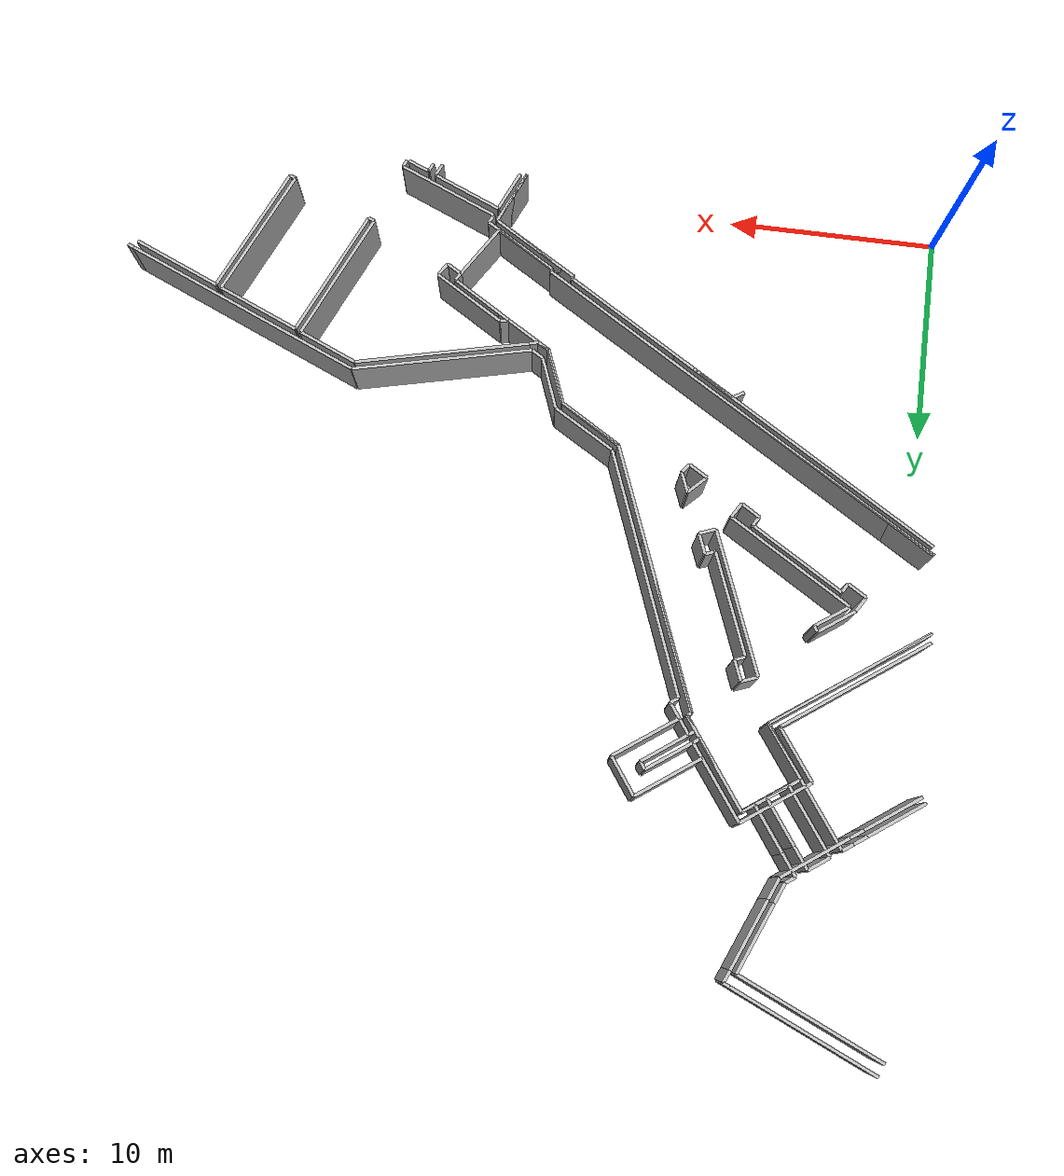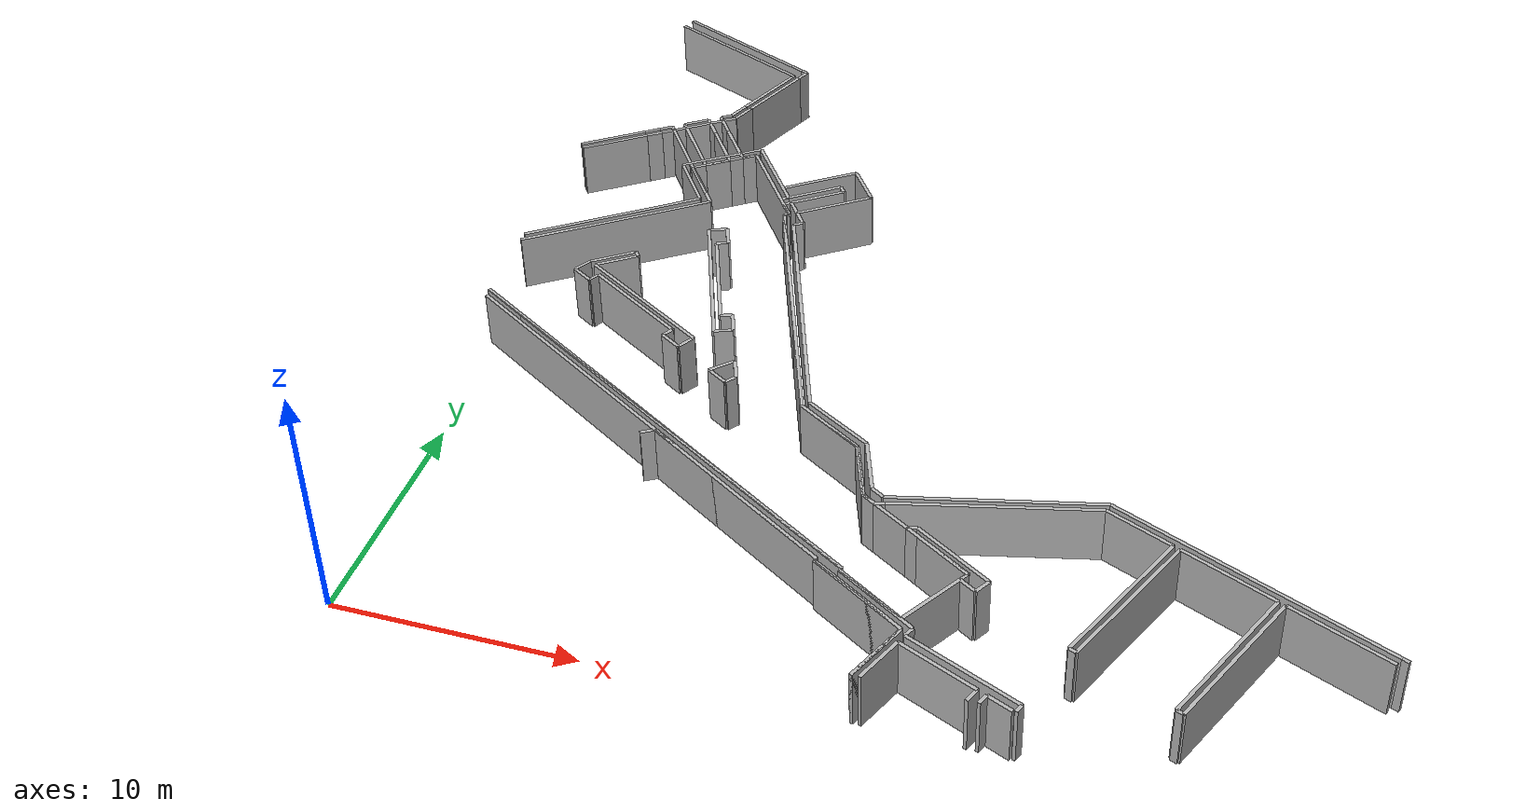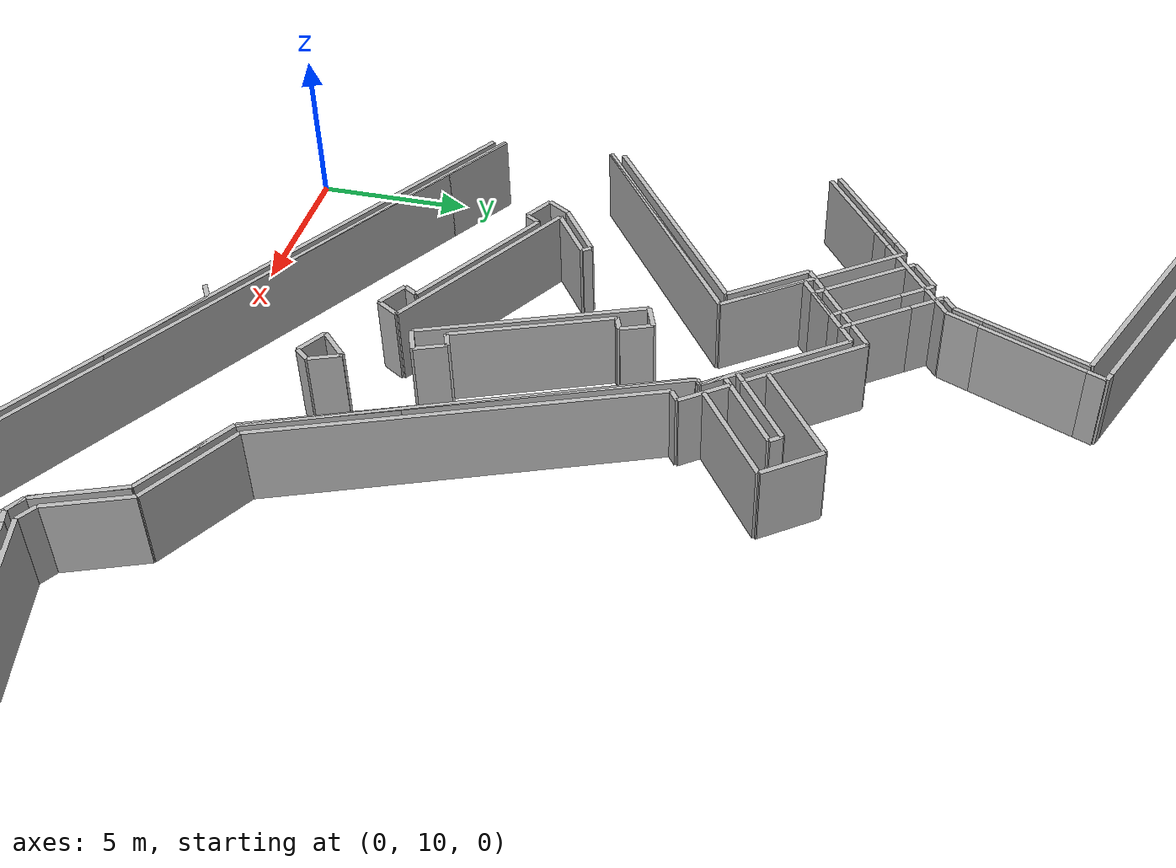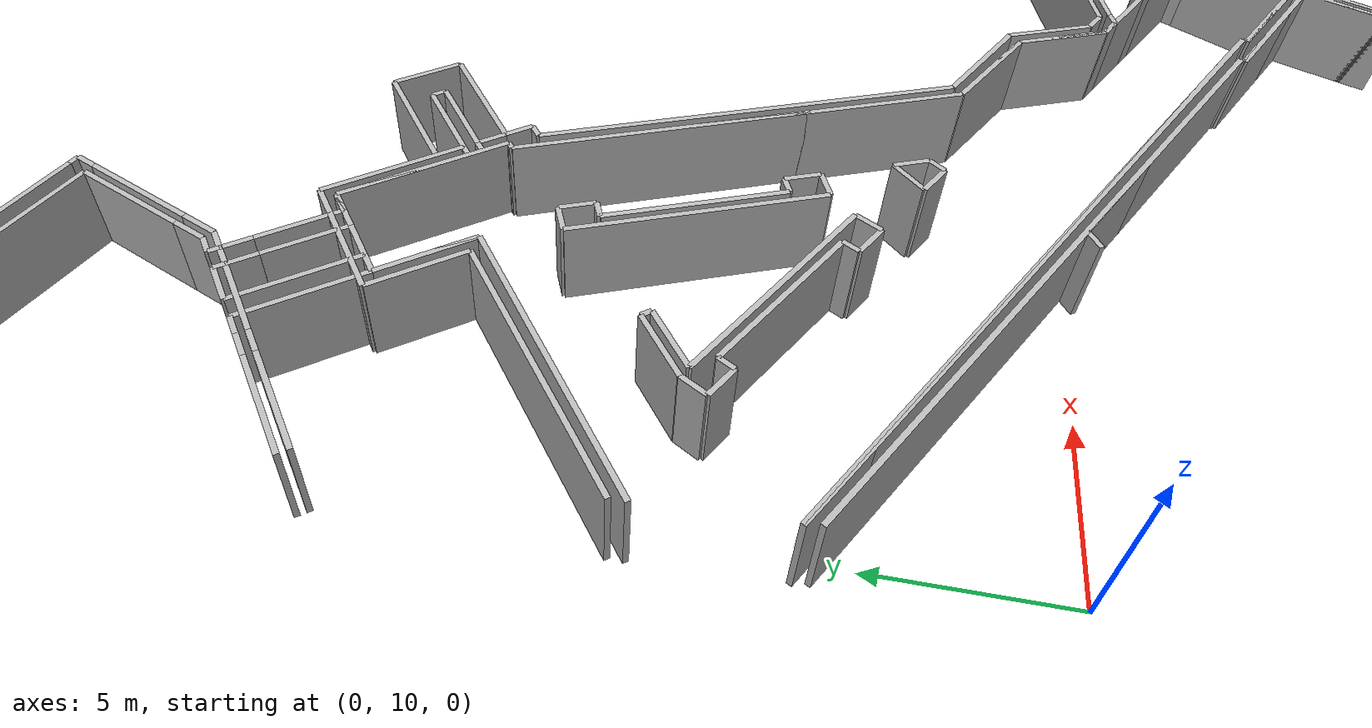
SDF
<?xml version="1.0" ?>
<sdf version="1.6">
  <model name="sps_1300">
    <pose frame="">0 0 0 0 -0 0</pose>
    <static>1</static>
    <self_collide>0</self_collide>
    <allow_auto_disable>0</allow_auto_disable>
    <link name="Wall177">
      <kinematic>0</kinematic>
      <gravity>1</gravity>
      <self_collide>0</self_collide>
      <collision name="collision">
        <geometry>
          <box>
            <size>3.49937 0.15 2.5</size>
          </box>
        </geometry>
        <pose frame="">0 0 0 0 -0 0</pose>
      </collision>
      <visual name="visual">
        <geometry>
          <box>
            <size>3.49937 0.15 2.5</size>
          </box>
        </geometry>
        <pose frame="">0 0 0 0 -0 0</pose>
        <cast_shadows>1</cast_shadows>
        <transparency>0.0</transparency>
      </visual>
      <pose frame="">22.96 1.26021 1.25 0 0 -0.398962</pose>
    </link>
    <link name="Wall178">
      <kinematic>0</kinematic>
      <gravity>1</gravity>
      <self_collide>0</self_collide>
      <collision name="collision">
        <geometry>
          <box>
            <size>4.15 0.15 2.5</size>
          </box>
        </geometry>
        <pose frame="">0 0 0 0 -0 0</pose>
      </collision>
      <visual name="visual">
        <geometry>
          <box>
            <size>4.15 0.15 2.5</size>
          </box>
        </geometry>
        <pose frame="">0 0 0 0 -0 0</pose>
        <cast_shadows>1</cast_shadows>
        <transparency>0.0</transparency>
      </visual>
      <pose frame="">31.8935 8.48128 1.25 0 0 -0.399139</pose>
    </link>
    <link name="Wall491">
      <kinematic>0</kinematic>
      <gravity>1</gravity>
      <self_collide>0</self_collide>
      <collision name="collision">
        <geometry>
          <box>
            <size>3.29186 0.15 2.5</size>
          </box>
        </geometry>
        <pose frame="">0 0 0 0 -0 0</pose>
      </collision>
      <visual name="visual">
        <geometry>
          <box>
            <size>3.29186 0.15 2.5</size>
          </box>
        </geometry>
        <pose frame="">0 0 0 0 -0 0</pose>
        <cast_shadows>1</cast_shadows>
        <transparency>0.0</transparency>
      </visual>
      <pose frame="">15.6525 12.1792 1.25 0 0 -0.547294</pose>
    </link>
    <link name="Wall492">
      <kinematic>0</kinematic>
      <gravity>1</gravity>
      <self_collide>0</self_collide>
      <collision name="collision">
        <geometry>
          <box>
            <size>0.125288 0.15 2.5</size>
          </box>
        </geometry>
        <pose frame="">0 0 0 0 -0 0</pose>
      </collision>
      <visual name="visual">
        <geometry>
          <box>
            <size>0.125288 0.15 2.5</size>
          </box>
        </geometry>
        <pose frame="">0 0 0 0 -0 0</pose>
        <cast_shadows>1</cast_shadows>
        <transparency>0.0</transparency>
      </visual>
      <pose frame="">17.3615 5.01298 1.25 0 -0 1.02361</pose>
    </link>
    <link name="Wall493">
      <kinematic>0</kinematic>
      <gravity>1</gravity>
      <self_collide>0</self_collide>
      <collision name="collision">
        <geometry>
          <box>
            <size>20.9807 0.15 2.5</size>
          </box>
        </geometry>
        <pose frame="">0 0 0 0 -0 0</pose>
      </collision>
      <visual name="visual">
        <geometry>
          <box>
            <size>20.9807 0.15 2.5</size>
          </box>
        </geometry>
        <pose frame="">0 0 0 0 -0 0</pose>
        <cast_shadows>1</cast_shadows>
        <transparency>0.0</transparency>
      </visual>
      <pose frame="">8.44585 10.5416 1.25 0 -0 2.59249</pose>
    </link>
    <link name="Wall496">
      <kinematic>0</kinematic>
      <gravity>1</gravity>
      <self_collide>0</self_collide>
      <collision name="collision">
        <geometry>
          <box>
            <size>22.2262 0.15 2.5</size>
          </box>
        </geometry>
        <pose frame="">0 0 0 0 -0 0</pose>
      </collision>
      <visual name="visual">
        <geometry>
          <box>
            <size>22.2262 0.15 2.5</size>
          </box>
        </geometry>
        <pose frame="">0 0 0 0 -0 0</pose>
        <cast_shadows>1</cast_shadows>
        <transparency>0.0</transparency>
      </visual>
      <pose frame="">8.93023 10.6325 1.25 0 -0 2.59411</pose>
    </link>
    <link name="Wall497">
      <kinematic>0</kinematic>
      <gravity>1</gravity>
      <self_collide>0</self_collide>
      <collision name="collision">
        <geometry>
          <box>
            <size>4.63862 0.15 2.5</size>
          </box>
        </geometry>
        <pose frame="">0 0 0 0 -0 0</pose>
      </collision>
      <visual name="visual">
        <geometry>
          <box>
            <size>4.63862 0.15 2.5</size>
          </box>
        </geometry>
        <pose frame="">0 0 0 0 -0 0</pose>
        <cast_shadows>1</cast_shadows>
        <transparency>0.0</transparency>
      </visual>
      <pose frame="">19.3144 3.7607 1.25 0 -0 2.5984</pose>
    </link>
    <link name="Wall498">
      <kinematic>0</kinematic>
      <gravity>1</gravity>
      <self_collide>0</self_collide>
      <collision name="collision">
        <geometry>
          <box>
            <size>0.629992 0.15 2.5</size>
          </box>
        </geometry>
        <pose frame="">0 0 0 0 -0 0</pose>
      </collision>
      <visual name="visual">
        <geometry>
          <box>
            <size>0.629992 0.15 2.5</size>
          </box>
        </geometry>
        <pose frame="">0 0 0 0 -0 0</pose>
        <cast_shadows>1</cast_shadows>
        <transparency>0.0</transparency>
      </visual>
      <pose frame="">24.4499 0.29026 1.25 0 0 -1.96974</pose>
    </link>
    <link name="Wall499">
      <kinematic>0</kinematic>
      <gravity>1</gravity>
      <self_collide>0</self_collide>
      <collision name="collision">
        <geometry>
          <box>
            <size>0.46109 0.15 2.5</size>
          </box>
        </geometry>
        <pose frame="">0 0 0 0 -0 0</pose>
      </collision>
      <visual name="visual">
        <geometry>
          <box>
            <size>0.46109 0.15 2.5</size>
          </box>
        </geometry>
        <pose frame="">0 0 0 0 -0 0</pose>
        <cast_shadows>1</cast_shadows>
        <transparency>0.0</transparency>
      </visual>
      <pose frame="">24.8511 0.21244 1.25 0 -0 1.17185</pose>
    </link>
    <link name="Wall500">
      <kinematic>0</kinematic>
      <gravity>1</gravity>
      <self_collide>0</self_collide>
      <collision name="collision">
        <geometry>
          <box>
            <size>0.354194 0.15 2.5</size>
          </box>
        </geometry>
        <pose frame="">0 0 0 0 -0 0</pose>
      </collision>
      <visual name="visual">
        <geometry>
          <box>
            <size>0.354194 0.15 2.5</size>
          </box>
        </geometry>
        <pose frame="">0 0 0 0 -0 0</pose>
        <cast_shadows>1</cast_shadows>
        <transparency>0.0</transparency>
      </visual>
      <pose frame="">26.133 0.163337 1.25 0 -0 1.174</pose>
    </link>
    <link name="Wall501">
      <kinematic>0</kinematic>
      <gravity>1</gravity>
      <self_collide>0</self_collide>
      <collision name="collision">
        <geometry>
          <box>
            <size>2.98287 0.15 2.5</size>
          </box>
        </geometry>
        <pose frame="">0 0 0 0 -0 0</pose>
      </collision>
      <visual name="visual">
        <geometry>
          <box>
            <size>2.98287 0.15 2.5</size>
          </box>
        </geometry>
        <pose frame="">0 0 0 0 -0 0</pose>
        <cast_shadows>1</cast_shadows>
        <transparency>0.0</transparency>
      </visual>
      <pose frame="">28.3314 9.98369 1.25 0 0 -0.39897</pose>
    </link>
    <link name="Wall502">
      <kinematic>0</kinematic>
      <gravity>1</gravity>
      <self_collide>0</self_collide>
      <collision name="collision">
        <geometry>
          <box>
            <size>6.57523 0.15 2.5</size>
          </box>
        </geometry>
        <pose frame="">0 0 0 0 -0 0</pose>
      </collision>
      <visual name="visual">
        <geometry>
          <box>
            <size>6.57523 0.15 2.5</size>
          </box>
        </geometry>
        <pose frame="">0 0 0 0 -0 0</pose>
        <cast_shadows>1</cast_shadows>
        <transparency>0.0</transparency>
      </visual>
      <pose frame="">28.7042 6.25838 1.25 0 -0 1.17174</pose>
    </link>
    <link name="Wall503">
      <kinematic>0</kinematic>
      <gravity>1</gravity>
      <self_collide>0</self_collide>
      <collision name="collision">
        <geometry>
          <box>
            <size>0.299765 0.15 2.5</size>
          </box>
        </geometry>
        <pose frame="">0 0 0 0 -0 0</pose>
      </collision>
      <visual name="visual">
        <geometry>
          <box>
            <size>0.299765 0.15 2.5</size>
          </box>
        </geometry>
        <pose frame="">0 0 0 0 -0 0</pose>
        <cast_shadows>1</cast_shadows>
        <transparency>0.0</transparency>
      </visual>
      <pose frame="">38.4624 6.10728 1.25 0 -0 2.74282</pose>
    </link>
    <link name="Wall783">
      <kinematic>0</kinematic>
      <gravity>1</gravity>
      <self_collide>0</self_collide>
      <collision name="collision">
        <geometry>
          <box>
            <size>0.633892 0.15 2.5</size>
          </box>
        </geometry>
        <pose frame="">0 0 0 0 -0 0</pose>
      </collision>
      <visual name="visual">
        <geometry>
          <box>
            <size>0.633892 0.15 2.5</size>
          </box>
        </geometry>
        <pose frame="">0 0 0 0 -0 0</pose>
        <cast_shadows>1</cast_shadows>
        <transparency>0.0</transparency>
      </visual>
      <pose frame="">18.5254 9.06819 1.25 0 0 -0.556058</pose>
    </link>
    <link name="Wall785">
      <kinematic>0</kinematic>
      <gravity>1</gravity>
      <self_collide>0</self_collide>
      <collision name="collision">
        <geometry>
          <box>
            <size>8.22723 0.15 2.5</size>
          </box>
        </geometry>
        <pose frame="">0 0 0 0 -0 0</pose>
      </collision>
      <visual name="visual">
        <geometry>
          <box>
            <size>8.22723 0.15 2.5</size>
          </box>
        </geometry>
        <pose frame="">0 0 0 0 -0 0</pose>
        <cast_shadows>1</cast_shadows>
        <transparency>0.0</transparency>
      </visual>
      <pose frame="">22.9618 9.58357 1.25 0 -0 0.240419</pose>
    </link>
    <link name="Wall1099">
      <kinematic>0</kinematic>
      <gravity>1</gravity>
      <self_collide>0</self_collide>
      <collision name="collision">
        <geometry>
          <box>
            <size>3.48771 0.15 2.5</size>
          </box>
        </geometry>
        <pose frame="">0 0 0 0 -0 0</pose>
      </collision>
      <visual name="visual">
        <geometry>
          <box>
            <size>3.48771 0.15 2.5</size>
          </box>
        </geometry>
        <pose frame="">0 0 0 0 -0 0</pose>
        <cast_shadows>1</cast_shadows>
        <transparency>0.0</transparency>
      </visual>
      <pose frame="">3.53826 28.6532 1.25 0 -0 2.19414</pose>
    </link>
    <link name="Wall1104">
      <kinematic>0</kinematic>
      <gravity>1</gravity>
      <self_collide>0</self_collide>
      <collision name="collision">
        <geometry>
          <box>
            <size>3.29762 0.15 2.5</size>
          </box>
        </geometry>
        <pose frame="">0 0 0 0 -0 0</pose>
      </collision>
      <visual name="visual">
        <geometry>
          <box>
            <size>3.29762 0.15 2.5</size>
          </box>
        </geometry>
        <pose frame="">0 0 0 0 -0 0</pose>
        <cast_shadows>1</cast_shadows>
        <transparency>0.0</transparency>
      </visual>
      <pose frame="">15.9271 12.448 1.25 0 0 -0.534338</pose>
    </link>
    <link name="Wall1105">
      <kinematic>0</kinematic>
      <gravity>1</gravity>
      <self_collide>0</self_collide>
      <collision name="collision">
        <geometry>
          <box>
            <size>2.54139 0.15 2.5</size>
          </box>
        </geometry>
        <pose frame="">0 0 0 0 -0 0</pose>
      </collision>
      <visual name="visual">
        <geometry>
          <box>
            <size>2.54139 0.15 2.5</size>
          </box>
        </geometry>
        <pose frame="">0 0 0 0 -0 0</pose>
        <cast_shadows>1</cast_shadows>
        <transparency>0.0</transparency>
      </visual>
      <pose frame="">17.8011 10.4219 1.25 0 0 -1.2045</pose>
    </link>
    <link name="Wall1107">
      <kinematic>0</kinematic>
      <gravity>1</gravity>
      <self_collide>0</self_collide>
      <collision name="collision">
        <geometry>
          <box>
            <size>2.10533 0.15 2.5</size>
          </box>
        </geometry>
        <pose frame="">0 0 0 0 -0 0</pose>
      </collision>
      <visual name="visual">
        <geometry>
          <box>
            <size>2.10533 0.15 2.5</size>
          </box>
        </geometry>
        <pose frame="">0 0 0 0 -0 0</pose>
        <cast_shadows>1</cast_shadows>
        <transparency>0.0</transparency>
      </visual>
      <pose frame="">20.9386 0.969947 1.25 0 -0 1.17172</pose>
    </link>
    <link name="Wall1108">
      <kinematic>0</kinematic>
      <gravity>1</gravity>
      <self_collide>0</self_collide>
      <collision name="collision">
        <geometry>
          <box>
            <size>3.88986 0.15 2.5</size>
          </box>
        </geometry>
        <pose frame="">0 0 0 0 -0 0</pose>
      </collision>
      <visual name="visual">
        <geometry>
          <box>
            <size>3.88986 0.15 2.5</size>
          </box>
        </geometry>
        <pose frame="">0 0 0 0 -0 0</pose>
        <cast_shadows>1</cast_shadows>
        <transparency>0.0</transparency>
      </visual>
      <pose frame="">20.0146 3.7285 1.25 0 -0 2.59425</pose>
    </link>
    <link name="Wall1109">
      <kinematic>0</kinematic>
      <gravity>1</gravity>
      <self_collide>0</self_collide>
      <collision name="collision">
        <geometry>
          <box>
            <size>6.57457 0.15 2.5</size>
          </box>
        </geometry>
        <pose frame="">0 0 0 0 -0 0</pose>
      </collision>
      <visual name="visual">
        <geometry>
          <box>
            <size>6.57457 0.15 2.5</size>
          </box>
        </geometry>
        <pose frame="">0 0 0 0 -0 0</pose>
        <cast_shadows>1</cast_shadows>
        <transparency>0.0</transparency>
      </visual>
      <pose frame="">32.5282 4.64589 1.25 0 0 -1.96986</pose>
    </link>
    <link name="Wall1110">
      <kinematic>0</kinematic>
      <gravity>1</gravity>
      <self_collide>0</self_collide>
      <collision name="collision">
        <geometry>
          <box>
            <size>12.23 0.15 2.5</size>
          </box>
        </geometry>
        <pose frame="">0 0 0 0 -0 0</pose>
      </collision>
      <visual name="visual">
        <geometry>
          <box>
            <size>12.23 0.15 2.5</size>
          </box>
        </geometry>
        <pose frame="">0 0 0 0 -0 0</pose>
        <cast_shadows>1</cast_shadows>
        <transparency>0.0</transparency>
      </visual>
      <pose frame="">32.687 8.53508 1.25 0 0 -0.397925</pose>
    </link>
    <link name="Wall1380">
      <kinematic>0</kinematic>
      <gravity>1</gravity>
      <self_collide>0</self_collide>
      <collision name="collision">
        <geometry>
          <box>
            <size>2.78321 0.15 2.5</size>
          </box>
        </geometry>
        <pose frame="">0 0 0 0 -0 0</pose>
      </collision>
      <visual name="visual">
        <geometry>
          <box>
            <size>2.78321 0.15 2.5</size>
          </box>
        </geometry>
        <pose frame="">0 0 0 0 -0 0</pose>
        <cast_shadows>1</cast_shadows>
        <transparency>0.0</transparency>
      </visual>
      <pose frame="">20.756 1.28095 1.25 0 -0 1.16932</pose>
    </link>
    <link name="Wall1381">
      <kinematic>0</kinematic>
      <gravity>1</gravity>
      <self_collide>0</self_collide>
      <collision name="collision">
        <geometry>
          <box>
            <size>0.442862 0.15 2.5</size>
          </box>
        </geometry>
        <pose frame="">0 0 0 0 -0 0</pose>
      </collision>
      <visual name="visual">
        <geometry>
          <box>
            <size>0.442862 0.15 2.5</size>
          </box>
        </geometry>
        <pose frame="">0 0 0 0 -0 0</pose>
        <cast_shadows>1</cast_shadows>
        <transparency>0.0</transparency>
      </visual>
      <pose frame="">21.5893 2.51231 1.25 0 -0 1.17148</pose>
    </link>
    <link name="Wall1383">
      <kinematic>0</kinematic>
      <gravity>1</gravity>
      <self_collide>0</self_collide>
      <collision name="collision">
        <geometry>
          <box>
            <size>5.099 0.15 2.5</size>
          </box>
        </geometry>
        <pose frame="">0 0 0 0 -0 0</pose>
      </collision>
      <visual name="visual">
        <geometry>
          <box>
            <size>5.099 0.15 2.5</size>
          </box>
        </geometry>
        <pose frame="">0 0 0 0 -0 0</pose>
        <cast_shadows>1</cast_shadows>
        <transparency>0.0</transparency>
      </visual>
      <pose frame="">23.8523 1.31749 1.25 0 -0 2.74245</pose>
    </link>
    <link name="Wall1385">
      <kinematic>0</kinematic>
      <gravity>1</gravity>
      <self_collide>0</self_collide>
      <collision name="collision">
        <geometry>
          <box>
            <size>0.299709 0.15 2.5</size>
          </box>
        </geometry>
        <pose frame="">0 0 0 0 -0 0</pose>
      </collision>
      <visual name="visual">
        <geometry>
          <box>
            <size>0.299709 0.15 2.5</size>
          </box>
        </geometry>
        <pose frame="">0 0 0 0 -0 0</pose>
        <cast_shadows>1</cast_shadows>
        <transparency>0.0</transparency>
      </visual>
      <pose frame="">27.2887 3.28728 1.25 0 0 -0.398848</pose>
    </link>
    <link name="Wall1386">
      <kinematic>0</kinematic>
      <gravity>1</gravity>
      <self_collide>0</self_collide>
      <collision name="collision">
        <geometry>
          <box>
            <size>6.57504 0.15 2.5</size>
          </box>
        </geometry>
        <pose frame="">0 0 0 0 -0 0</pose>
      </collision>
      <visual name="visual">
        <geometry>
          <box>
            <size>6.57504 0.15 2.5</size>
          </box>
        </geometry>
        <pose frame="">0 0 0 0 -0 0</pose>
        <cast_shadows>1</cast_shadows>
        <transparency>0.0</transparency>
      </visual>
      <pose frame="">32.805 4.52949 1.25 0 -0 1.17157</pose>
    </link>
    <link name="Wall1704">
      <kinematic>0</kinematic>
      <gravity>1</gravity>
      <self_collide>0</self_collide>
      <collision name="collision">
        <geometry>
          <box>
            <size>1.09212 0.15 2.5</size>
          </box>
        </geometry>
        <pose frame="">0 0 0 0 -0 0</pose>
      </collision>
      <visual name="visual">
        <geometry>
          <box>
            <size>1.09212 0.15 2.5</size>
          </box>
        </geometry>
        <pose frame="">0 0 0 0 -0 0</pose>
        <cast_shadows>1</cast_shadows>
        <transparency>0.0</transparency>
      </visual>
      <pose frame="">25.4437 0.21244 1.25 0 0 -0.399592</pose>
    </link>
    <link name="Wall1995">
      <kinematic>0</kinematic>
      <gravity>1</gravity>
      <self_collide>0</self_collide>
      <collision name="collision">
        <geometry>
          <box>
            <size>2.70944 0.15 2.5</size>
          </box>
        </geometry>
        <pose frame="">0 0 0 0 -0 0</pose>
      </collision>
      <visual name="visual">
        <geometry>
          <box>
            <size>2.70944 0.15 2.5</size>
          </box>
        </geometry>
        <pose frame="">0 0 0 0 -0 0</pose>
        <cast_shadows>1</cast_shadows>
        <transparency>0.0</transparency>
      </visual>
      <pose frame="">17.5489 10.06 1.25 0 0 -1.20009</pose>
    </link>
    <link name="Wall1996">
      <kinematic>0</kinematic>
      <gravity>1</gravity>
      <self_collide>0</self_collide>
      <collision name="collision">
        <geometry>
          <box>
            <size>0.125288 0.15 2.5</size>
          </box>
        </geometry>
        <pose frame="">0 0 0 0 -0 0</pose>
      </collision>
      <visual name="visual">
        <geometry>
          <box>
            <size>0.125288 0.15 2.5</size>
          </box>
        </geometry>
        <pose frame="">0 0 0 0 -0 0</pose>
        <cast_shadows>1</cast_shadows>
        <transparency>0.0</transparency>
      </visual>
      <pose frame="">18.3864 4.79417 1.25 0 -0 1.02361</pose>
    </link>
    <link name="Wall1997">
      <kinematic>0</kinematic>
      <gravity>1</gravity>
      <self_collide>0</self_collide>
      <collision name="collision">
        <geometry>
          <box>
            <size>0.610297 0.15 2.5</size>
          </box>
        </geometry>
        <pose frame="">0 0 0 0 -0 0</pose>
      </collision>
      <visual name="visual">
        <geometry>
          <box>
            <size>0.610297 0.15 2.5</size>
          </box>
        </geometry>
        <pose frame="">0 0 0 0 -0 0</pose>
        <cast_shadows>1</cast_shadows>
        <transparency>0.0</transparency>
      </visual>
      <pose frame="">18.3003 8.63859 1.25 0 0 -0.547023</pose>
    </link>
    <link name="Wall2000">
      <kinematic>0</kinematic>
      <gravity>1</gravity>
      <self_collide>0</self_collide>
      <collision name="collision">
        <geometry>
          <box>
            <size>8.4949 0.15 2.5</size>
          </box>
        </geometry>
        <pose frame="">0 0 0 0 -0 0</pose>
      </collision>
      <visual name="visual">
        <geometry>
          <box>
            <size>8.4949 0.15 2.5</size>
          </box>
        </geometry>
        <pose frame="">0 0 0 0 -0 0</pose>
        <cast_shadows>1</cast_shadows>
        <transparency>0.0</transparency>
      </visual>
      <pose frame="">22.9222 9.90279 1.25 0 -0 0.238125</pose>
    </link>
    <link name="Wall2001">
      <kinematic>0</kinematic>
      <gravity>1</gravity>
      <self_collide>0</self_collide>
      <collision name="collision">
        <geometry>
          <box>
            <size>6.57552 0.15 2.5</size>
          </box>
        </geometry>
        <pose frame="">0 0 0 0 -0 0</pose>
      </collision>
      <visual name="visual">
        <geometry>
          <box>
            <size>6.57552 0.15 2.5</size>
          </box>
        </geometry>
        <pose frame="">0 0 0 0 -0 0</pose>
        <cast_shadows>1</cast_shadows>
        <transparency>0.0</transparency>
      </visual>
      <pose frame="">28.4282 6.37489 1.25 0 0 -1.96987</pose>
    </link>
    <link name="Wall2334">
      <kinematic>0</kinematic>
      <gravity>1</gravity>
      <self_collide>0</self_collide>
      <collision name="collision">
        <geometry>
          <box>
            <size>0.424171 0.15 2.5</size>
          </box>
        </geometry>
        <pose frame="">0 0 0 0 -0 0</pose>
      </collision>
      <visual name="visual">
        <geometry>
          <box>
            <size>0.424171 0.15 2.5</size>
          </box>
        </geometry>
        <pose frame="">0 0 0 0 -0 0</pose>
        <cast_shadows>1</cast_shadows>
        <transparency>0.0</transparency>
      </visual>
      <pose frame="">18.7637 8.54198 1.25 0 -0 0.297177</pose>
    </link>
    <link name="Wall2335">
      <kinematic>0</kinematic>
      <gravity>1</gravity>
      <self_collide>0</self_collide>
      <collision name="collision">
        <geometry>
          <box>
            <size>0.299709 0.15 2.5</size>
          </box>
        </geometry>
        <pose frame="">0 0 0 0 -0 0</pose>
      </collision>
      <visual name="visual">
        <geometry>
          <box>
            <size>0.299709 0.15 2.5</size>
          </box>
        </geometry>
        <pose frame="">0 0 0 0 -0 0</pose>
        <cast_shadows>1</cast_shadows>
        <transparency>0.0</transparency>
      </visual>
      <pose frame="">31.389 1.5587 1.25 0 0 -0.398848</pose>
    </link>
    <link name="Wall2336">
      <kinematic>0</kinematic>
      <gravity>1</gravity>
      <self_collide>0</self_collide>
      <collision name="collision">
        <geometry>
          <box>
            <size>4.4497 0.15 2.5</size>
          </box>
        </geometry>
        <pose frame="">0 0 0 0 -0 0</pose>
      </collision>
      <visual name="visual">
        <geometry>
          <box>
            <size>4.4497 0.15 2.5</size>
          </box>
        </geometry>
        <pose frame="">0 0 0 0 -0 0</pose>
        <cast_shadows>1</cast_shadows>
        <transparency>0.0</transparency>
      </visual>
      <pose frame="">36.1327 6.69368 1.25 0 0 -0.399224</pose>
    </link>
    <link name="Wall12707">
      <kinematic>0</kinematic>
      <gravity>1</gravity>
      <self_collide>0</self_collide>
      <collision name="collision">
        <geometry>
          <box>
            <size>8.4805 0.15 2.5</size>
          </box>
        </geometry>
        <pose frame="">0 0 0 0 -0 0</pose>
      </collision>
      <visual name="visual">
        <geometry>
          <box>
            <size>8.4805 0.15 2.5</size>
          </box>
        </geometry>
        <pose frame="">0 0 0 0 -0 0</pose>
        <cast_shadows>1</cast_shadows>
        <transparency>0.0</transparency>
      </visual>
      <pose frame="">2.74746 22.4891 1.25 0 -0 0.623261</pose>
    </link>
    <link name="Wall12708">
      <kinematic>0</kinematic>
      <gravity>1</gravity>
      <self_collide>0</self_collide>
      <collision name="collision">
        <geometry>
          <box>
            <size>2.79971 0.15 2.5</size>
          </box>
        </geometry>
        <pose frame="">0 0 0 0 -0 0</pose>
      </collision>
      <visual name="visual">
        <geometry>
          <box>
            <size>2.79971 0.15 2.5</size>
          </box>
        </geometry>
        <pose frame="">0 0 0 0 -0 0</pose>
        <cast_shadows>1</cast_shadows>
        <transparency>0.0</transparency>
      </visual>
      <pose frame="">5.37334 26.1007 1.25 0 -0 2.19409</pose>
    </link>
    <link name="Wall12709">
      <kinematic>0</kinematic>
      <gravity>1</gravity>
      <self_collide>0</self_collide>
      <collision name="collision">
        <geometry>
          <box>
            <size>2.99978 0.15 2.5</size>
          </box>
        </geometry>
        <pose frame="">0 0 0 0 -0 0</pose>
      </collision>
      <visual name="visual">
        <geometry>
          <box>
            <size>2.99978 0.15 2.5</size>
          </box>
        </geometry>
        <pose frame="">0 0 0 0 -0 0</pose>
        <cast_shadows>1</cast_shadows>
        <transparency>0.0</transparency>
      </visual>
      <pose frame="">5.77395 28.113 1.25 0 -0 0.623454</pose>
    </link>
    <link name="Wall12710">
      <kinematic>0</kinematic>
      <gravity>1</gravity>
      <self_collide>0</self_collide>
      <collision name="collision">
        <geometry>
          <box>
            <size>4.79995 0.15 2.5</size>
          </box>
        </geometry>
        <pose frame="">0 0 0 0 -0 0</pose>
      </collision>
      <visual name="visual">
        <geometry>
          <box>
            <size>4.79995 0.15 2.5</size>
          </box>
        </geometry>
        <pose frame="">0 0 0 0 -0 0</pose>
        <cast_shadows>1</cast_shadows>
        <transparency>0.0</transparency>
      </visual>
      <pose frame="">8.39266 27.0401 1.25 0 0 -0.947449</pose>
    </link>
    <link name="Wall12711">
      <kinematic>0</kinematic>
      <gravity>1</gravity>
      <self_collide>0</self_collide>
      <collision name="collision">
        <geometry>
          <box>
            <size>0.22534 0.15 2.5</size>
          </box>
        </geometry>
        <pose frame="">0 0 0 0 -0 0</pose>
      </collision>
      <visual name="visual">
        <geometry>
          <box>
            <size>0.22534 0.15 2.5</size>
          </box>
        </geometry>
        <pose frame="">0 0 0 0 -0 0</pose>
        <cast_shadows>1</cast_shadows>
        <transparency>0.0</transparency>
      </visual>
      <pose frame="">9.70235 25.0255 1.25 0 0 -2.51564</pose>
    </link>
    <link name="Wall12712">
      <kinematic>0</kinematic>
      <gravity>1</gravity>
      <self_collide>0</self_collide>
      <collision name="collision">
        <geometry>
          <box>
            <size>12.7933 0.15 2.5</size>
          </box>
        </geometry>
        <pose frame="">0 0 0 0 -0 0</pose>
      </collision>
      <visual name="visual">
        <geometry>
          <box>
            <size>12.7933 0.15 2.5</size>
          </box>
        </geometry>
        <pose frame="">0 0 0 0 -0 0</pose>
        <cast_shadows>1</cast_shadows>
        <transparency>0.0</transparency>
      </visual>
      <pose frame="">11.9293 18.9977 1.25 0 0 -1.19994</pose>
    </link>
    <link name="Wall12713">
      <kinematic>0</kinematic>
      <gravity>1</gravity>
      <self_collide>0</self_collide>
      <collision name="collision">
        <geometry>
          <box>
            <size>3.29175 0.15 2.5</size>
          </box>
        </geometry>
        <pose frame="">0 0 0 0 -0 0</pose>
      </collision>
      <visual name="visual">
        <geometry>
          <box>
            <size>3.29175 0.15 2.5</size>
          </box>
        </geometry>
        <pose frame="">0 0 0 0 -0 0</pose>
        <cast_shadows>1</cast_shadows>
        <transparency>0.0</transparency>
      </visual>
      <pose frame="">15.6529 12.1793 1.25 0 0 -0.54738</pose>
    </link>
    <link name="Wall12714">
      <kinematic>0</kinematic>
      <gravity>1</gravity>
      <self_collide>0</self_collide>
      <collision name="collision">
        <geometry>
          <box>
            <size>2.70929 0.15 2.5</size>
          </box>
        </geometry>
        <pose frame="">0 0 0 0 -0 0</pose>
      </collision>
      <visual name="visual">
        <geometry>
          <box>
            <size>2.70929 0.15 2.5</size>
          </box>
        </geometry>
        <pose frame="">0 0 0 0 -0 0</pose>
        <cast_shadows>1</cast_shadows>
        <transparency>0.0</transparency>
      </visual>
      <pose frame="">17.5491 10.0601 1.25 0 0 -1.20004</pose>
    </link>
    <link name="Wall12715">
      <kinematic>0</kinematic>
      <gravity>1</gravity>
      <self_collide>0</self_collide>
      <collision name="collision">
        <geometry>
          <box>
            <size>0.61034 0.15 2.5</size>
          </box>
        </geometry>
        <pose frame="">0 0 0 0 -0 0</pose>
      </collision>
      <visual name="visual">
        <geometry>
          <box>
            <size>0.61034 0.15 2.5</size>
          </box>
        </geometry>
        <pose frame="">0 0 0 0 -0 0</pose>
        <cast_shadows>1</cast_shadows>
        <transparency>0.0</transparency>
      </visual>
      <pose frame="">18.3005 8.63869 1.25 0 0 -0.547331</pose>
    </link>
    <link name="Wall12716">
      <kinematic>0</kinematic>
      <gravity>1</gravity>
      <self_collide>0</self_collide>
      <collision name="collision">
        <geometry>
          <box>
            <size>1.78766 0.15 2.5</size>
          </box>
        </geometry>
        <pose frame="">0 0 0 0 -0 0</pose>
      </collision>
      <visual name="visual">
        <geometry>
          <box>
            <size>1.78766 0.15 2.5</size>
          </box>
        </geometry>
        <pose frame="">0 0 0 0 -0 0</pose>
        <cast_shadows>1</cast_shadows>
        <transparency>0.0</transparency>
      </visual>
      <pose frame="">19.3267 8.01857 1.25 0 0 -0.542287</pose>
    </link>
    <link name="Wall12717">
      <kinematic>0</kinematic>
      <gravity>1</gravity>
      <self_collide>0</self_collide>
      <collision name="collision">
        <geometry>
          <box>
            <size>3.24953 0.15 2.5</size>
          </box>
        </geometry>
        <pose frame="">0 0 0 0 -0 0</pose>
      </collision>
      <visual name="visual">
        <geometry>
          <box>
            <size>3.24953 0.15 2.5</size>
          </box>
        </geometry>
        <pose frame="">0 0 0 0 -0 0</pose>
        <cast_shadows>1</cast_shadows>
        <transparency>0.0</transparency>
      </visual>
      <pose frame="">21.477 6.70729 1.25 0 0 -0.550528</pose>
    </link>
    <link name="Wall12718">
      <kinematic>0</kinematic>
      <gravity>1</gravity>
      <self_collide>0</self_collide>
      <collision name="collision">
        <geometry>
          <box>
            <size>0.399737 0.15 2.5</size>
          </box>
        </geometry>
        <pose frame="">0 0 0 0 -0 0</pose>
      </collision>
      <visual name="visual">
        <geometry>
          <box>
            <size>0.399737 0.15 2.5</size>
          </box>
        </geometry>
        <pose frame="">0 0 0 0 -0 0</pose>
        <cast_shadows>1</cast_shadows>
        <transparency>0.0</transparency>
      </visual>
      <pose frame="">22.7579 5.68651 1.25 0 0 -2.11682</pose>
    </link>
    <link name="Wall12719">
      <kinematic>0</kinematic>
      <gravity>1</gravity>
      <self_collide>0</self_collide>
      <collision name="collision">
        <geometry>
          <box>
            <size>2.89947 0.15 2.5</size>
          </box>
        </geometry>
        <pose frame="">0 0 0 0 -0 0</pose>
      </collision>
      <visual name="visual">
        <geometry>
          <box>
            <size>2.89947 0.15 2.5</size>
          </box>
        </geometry>
        <pose frame="">0 0 0 0 -0 0</pose>
        <cast_shadows>1</cast_shadows>
        <transparency>0.0</transparency>
      </visual>
      <pose frame="">21.8996 4.27779 1.25 0 0 -2.11818</pose>
    </link>
    <link name="Wall12720">
      <kinematic>0</kinematic>
      <gravity>1</gravity>
      <self_collide>0</self_collide>
      <collision name="collision">
        <geometry>
          <box>
            <size>3.26869 0.15 2.5</size>
          </box>
        </geometry>
        <pose frame="">0 0 0 0 -0 0</pose>
      </collision>
      <visual name="visual">
        <geometry>
          <box>
            <size>3.26869 0.15 2.5</size>
          </box>
        </geometry>
        <pose frame="">0 0 0 0 -0 0</pose>
        <cast_shadows>1</cast_shadows>
        <transparency>0.0</transparency>
      </visual>
      <pose frame="">19.7494 3.8904 1.25 0 -0 2.59427</pose>
    </link>
    <link name="Wall12721">
      <kinematic>0</kinematic>
      <gravity>1</gravity>
      <self_collide>0</self_collide>
      <collision name="collision">
        <geometry>
          <box>
            <size>0.125288 0.15 2.5</size>
          </box>
        </geometry>
        <pose frame="">0 0 0 0 -0 0</pose>
      </collision>
      <visual name="visual">
        <geometry>
          <box>
            <size>0.125288 0.15 2.5</size>
          </box>
        </geometry>
        <pose frame="">0 0 0 0 -0 0</pose>
        <cast_shadows>1</cast_shadows>
        <transparency>0.0</transparency>
      </visual>
      <pose frame="">18.3864 4.79442 1.25 0 -0 1.02361</pose>
    </link>
    <link name="Wall12722">
      <kinematic>0</kinematic>
      <gravity>1</gravity>
      <self_collide>0</self_collide>
      <collision name="collision">
        <geometry>
          <box>
            <size>22.2261 0.15 2.5</size>
          </box>
        </geometry>
        <pose frame="">0 0 0 0 -0 0</pose>
      </collision>
      <visual name="visual">
        <geometry>
          <box>
            <size>22.2261 0.15 2.5</size>
          </box>
        </geometry>
        <pose frame="">0 0 0 0 -0 0</pose>
        <cast_shadows>1</cast_shadows>
        <transparency>0.0</transparency>
      </visual>
      <pose frame="">8.93023 10.6326 1.25 0 -0 2.59412</pose>
    </link>
    <link name="Wall15450">
      <kinematic>0</kinematic>
      <gravity>1</gravity>
      <self_collide>0</self_collide>
      <collision name="collision">
        <geometry>
          <box>
            <size>7.87621 0.15 2.5</size>
          </box>
        </geometry>
        <pose frame="">0 0 0 0 -0 0</pose>
      </collision>
      <visual name="visual">
        <geometry>
          <box>
            <size>7.87621 0.15 2.5</size>
          </box>
        </geometry>
        <pose frame="">0 0 0 0 -0 0</pose>
        <cast_shadows>1</cast_shadows>
        <transparency>0.0</transparency>
      </visual>
      <pose frame="">2.48925 22.7498 1.25 0 -0 0.62805</pose>
    </link>
    <link name="Wall15451">
      <kinematic>0</kinematic>
      <gravity>1</gravity>
      <self_collide>0</self_collide>
      <collision name="collision">
        <geometry>
          <box>
            <size>2.77886 0.15 2.5</size>
          </box>
        </geometry>
        <pose frame="">0 0 0 0 -0 0</pose>
      </collision>
      <visual name="visual">
        <geometry>
          <box>
            <size>2.77886 0.15 2.5</size>
          </box>
        </geometry>
        <pose frame="">0 0 0 0 -0 0</pose>
        <cast_shadows>1</cast_shadows>
        <transparency>0.0</transparency>
      </visual>
      <pose frame="">4.86477 26.1918 1.25 0 -0 2.19415</pose>
    </link>
    <link name="Wall15452">
      <kinematic>0</kinematic>
      <gravity>1</gravity>
      <self_collide>0</self_collide>
      <collision name="collision">
        <geometry>
          <box>
            <size>3.68895 0.15 2.5</size>
          </box>
        </geometry>
        <pose frame="">0 0 0 0 -0 0</pose>
      </collision>
      <visual name="visual">
        <geometry>
          <box>
            <size>3.68895 0.15 2.5</size>
          </box>
        </geometry>
        <pose frame="">0 0 0 0 -0 0</pose>
        <cast_shadows>1</cast_shadows>
        <transparency>0.0</transparency>
      </visual>
      <pose frame="">5.55486 28.3916 1.25 0 -0 0.619988</pose>
    </link>
    <link name="Wall15453">
      <kinematic>0</kinematic>
      <gravity>1</gravity>
      <self_collide>0</self_collide>
      <collision name="collision">
        <geometry>
          <box>
            <size>3.98487 0.15 2.5</size>
          </box>
        </geometry>
        <pose frame="">0 0 0 0 -0 0</pose>
      </collision>
      <visual name="visual">
        <geometry>
          <box>
            <size>3.98487 0.15 2.5</size>
          </box>
        </geometry>
        <pose frame="">0 0 0 0 -0 0</pose>
        <cast_shadows>1</cast_shadows>
        <transparency>0.0</transparency>
      </visual>
      <pose frame="">8.22857 27.8524 1.25 0 0 -0.941614</pose>
    </link>
    <link name="Wall22045">
      <kinematic>0</kinematic>
      <gravity>1</gravity>
      <self_collide>0</self_collide>
      <collision name="collision">
        <geometry>
          <box>
            <size>1.00012 0.15 2.5</size>
          </box>
        </geometry>
        <pose frame="">0 0 0 0 -0 0</pose>
      </collision>
      <visual name="visual">
        <geometry>
          <box>
            <size>1.00012 0.15 2.5</size>
          </box>
        </geometry>
        <pose frame="">0 0 0 0 -0 0</pose>
        <cast_shadows>1</cast_shadows>
        <transparency>0.0</transparency>
      </visual>
      <pose frame="">2.77953 18.482 1.25 0 0 -0.547013</pose>
    </link>
    <link name="Wall22046">
      <kinematic>0</kinematic>
      <gravity>1</gravity>
      <self_collide>0</self_collide>
      <collision name="collision">
        <geometry>
          <box>
            <size>0.500063 0.15 2.5</size>
          </box>
        </geometry>
        <pose frame="">0 0 0 0 -0 0</pose>
      </collision>
      <visual name="visual">
        <geometry>
          <box>
            <size>0.500063 0.15 2.5</size>
          </box>
        </geometry>
        <pose frame="">0 0 0 0 -0 0</pose>
        <cast_shadows>1</cast_shadows>
        <transparency>0.0</transparency>
      </visual>
      <pose frame="">3.33675 18.4354 1.25 0 -0 1.02343</pose>
    </link>
    <link name="Wall22047">
      <kinematic>0</kinematic>
      <gravity>1</gravity>
      <self_collide>0</self_collide>
      <collision name="collision">
        <geometry>
          <box>
            <size>5.00003 0.15 2.5</size>
          </box>
        </geometry>
        <pose frame="">0 0 0 0 -0 0</pose>
      </collision>
      <visual name="visual">
        <geometry>
          <box>
            <size>5.00003 0.15 2.5</size>
          </box>
        </geometry>
        <pose frame="">0 0 0 0 -0 0</pose>
        <cast_shadows>1</cast_shadows>
        <transparency>0.0</transparency>
      </visual>
      <pose frame="">5.60146 17.3475 1.25 0 0 -0.5475</pose>
    </link>
    <link name="Wall22048">
      <kinematic>0</kinematic>
      <gravity>1</gravity>
      <self_collide>0</self_collide>
      <collision name="collision">
        <geometry>
          <box>
            <size>0.500092 0.15 2.5</size>
          </box>
        </geometry>
        <pose frame="">0 0 0 0 -0 0</pose>
      </collision>
      <visual name="visual">
        <geometry>
          <box>
            <size>0.500092 0.15 2.5</size>
          </box>
        </geometry>
        <pose frame="">0 0 0 0 -0 0</pose>
        <cast_shadows>1</cast_shadows>
        <transparency>0.0</transparency>
      </visual>
      <pose frame="">7.60604 15.8325 1.25 0 0 -2.11756</pose>
    </link>
    <link name="Wall22049">
      <kinematic>0</kinematic>
      <gravity>1</gravity>
      <self_collide>0</self_collide>
      <collision name="collision">
        <geometry>
          <box>
            <size>0.999859 0.15 2.5</size>
          </box>
        </geometry>
        <pose frame="">0 0 0 0 -0 0</pose>
      </collision>
      <visual name="visual">
        <geometry>
          <box>
            <size>0.999859 0.15 2.5</size>
          </box>
        </geometry>
        <pose frame="">0 0 0 0 -0 0</pose>
        <cast_shadows>1</cast_shadows>
        <transparency>0.0</transparency>
      </visual>
      <pose frame="">7.90273 15.3584 1.25 0 0 -0.548104</pose>
    </link>
    <link name="Wall22050">
      <kinematic>0</kinematic>
      <gravity>1</gravity>
      <self_collide>0</self_collide>
      <collision name="collision">
        <geometry>
          <box>
            <size>0.800548 0.15 2.5</size>
          </box>
        </geometry>
        <pose frame="">0 0 0 0 -0 0</pose>
      </collision>
      <visual name="visual">
        <geometry>
          <box>
            <size>0.800548 0.15 2.5</size>
          </box>
        </geometry>
        <pose frame="">0 0 0 0 -0 0</pose>
        <cast_shadows>1</cast_shadows>
        <transparency>0.0</transparency>
      </visual>
      <pose frame="">8.53774 15.4397 1.25 0 -0 1.02345</pose>
    </link>
    <link name="Wall22051">
      <kinematic>0</kinematic>
      <gravity>1</gravity>
      <self_collide>0</self_collide>
      <collision name="collision">
        <geometry>
          <box>
            <size>6.67435 0.15 2.5</size>
          </box>
        </geometry>
        <pose frame="">0 0 0 0 -0 0</pose>
      </collision>
      <visual name="visual">
        <geometry>
          <box>
            <size>6.67435 0.15 2.5</size>
          </box>
        </geometry>
        <pose frame="">0 0 0 0 -0 0</pose>
        <cast_shadows>1</cast_shadows>
        <transparency>0.0</transparency>
      </visual>
      <pose frame="">5.89657 17.5185 1.25 0 -0 2.59416</pose>
    </link>
    <link name="Wall22052">
      <kinematic>0</kinematic>
      <gravity>1</gravity>
      <self_collide>0</self_collide>
      <collision name="collision">
        <geometry>
          <box>
            <size>1.87382 0.15 2.5</size>
          </box>
        </geometry>
        <pose frame="">0 0 0 0 -0 0</pose>
      </collision>
      <visual name="visual">
        <geometry>
          <box>
            <size>1.87382 0.15 2.5</size>
          </box>
        </geometry>
        <pose frame="">0 0 0 0 -0 0</pose>
        <cast_shadows>1</cast_shadows>
        <transparency>0.0</transparency>
      </visual>
      <pose frame="">3.80767 19.8026 1.25 0 -0 0.623559</pose>
    </link>
    <link name="Wall22053">
      <kinematic>0</kinematic>
      <gravity>1</gravity>
      <self_collide>0</self_collide>
      <collision name="collision">
        <geometry>
          <box>
            <size>0.299494 0.15 2.5</size>
          </box>
        </geometry>
        <pose frame="">0 0 0 0 -0 0</pose>
      </collision>
      <visual name="visual">
        <geometry>
          <box>
            <size>0.299494 0.15 2.5</size>
          </box>
        </geometry>
        <pose frame="">0 0 0 0 -0 0</pose>
        <cast_shadows>1</cast_shadows>
        <transparency>0.0</transparency>
      </visual>
      <pose frame="">4.48046 20.471 1.25 0 -0 2.1973</pose>
    </link>
    <link name="Wall22054">
      <kinematic>0</kinematic>
      <gravity>1</gravity>
      <self_collide>0</self_collide>
      <collision name="collision">
        <geometry>
          <box>
            <size>1.99912 0.15 2.5</size>
          </box>
        </geometry>
        <pose frame="">0 0 0 0 -0 0</pose>
      </collision>
      <visual name="visual">
        <geometry>
          <box>
            <size>1.99912 0.15 2.5</size>
          </box>
        </geometry>
        <pose frame="">0 0 0 0 -0 0</pose>
        <cast_shadows>1</cast_shadows>
        <transparency>0.0</transparency>
      </visual>
      <pose frame="">3.58095 20.009 1.25 0 0 -2.51848</pose>
    </link>
    <link name="Wall22055">
      <kinematic>0</kinematic>
      <gravity>1</gravity>
      <self_collide>0</self_collide>
      <collision name="collision">
        <geometry>
          <box>
            <size>0.800644 0.15 2.5</size>
          </box>
        </geometry>
        <pose frame="">0 0 0 0 -0 0</pose>
      </collision>
      <visual name="visual">
        <geometry>
          <box>
            <size>0.800644 0.15 2.5</size>
          </box>
        </geometry>
        <pose frame="">0 0 0 0 -0 0</pose>
        <cast_shadows>1</cast_shadows>
        <transparency>0.0</transparency>
      </visual>
      <pose frame="">2.56084 19.0839 1.25 0 0 -2.11834</pose>
    </link>
    <link name="Wall22056">
      <kinematic>0</kinematic>
      <gravity>1</gravity>
      <self_collide>0</self_collide>
      <collision name="collision">
        <geometry>
          <box>
            <size>0.672337 0.15 2.5</size>
          </box>
        </geometry>
        <pose frame="">0 0 0 0 -0 0</pose>
      </collision>
      <visual name="visual">
        <geometry>
          <box>
            <size>0.672337 0.15 2.5</size>
          </box>
        </geometry>
        <pose frame="">0 0 0 0 -0 0</pose>
        <cast_shadows>1</cast_shadows>
        <transparency>0.0</transparency>
      </visual>
      <pose frame="">6.71914 28.7926 1.25 0 -0 0.623637</pose>
    </link>
    <link name="Wall22057">
      <kinematic>0</kinematic>
      <gravity>1</gravity>
      <self_collide>0</self_collide>
      <collision name="collision">
        <geometry>
          <box>
            <size>3.63868 0.15 2.5</size>
          </box>
        </geometry>
        <pose frame="">0 0 0 0 -0 0</pose>
      </collision>
      <visual name="visual">
        <geometry>
          <box>
            <size>3.63868 0.15 2.5</size>
          </box>
        </geometry>
        <pose frame="">0 0 0 0 -0 0</pose>
        <cast_shadows>1</cast_shadows>
        <transparency>0.0</transparency>
      </visual>
      <pose frame="">8.05404 27.5117 1.25 0 0 -0.947476</pose>
    </link>
    <link name="Wall22070">
      <kinematic>0</kinematic>
      <gravity>1</gravity>
      <self_collide>0</self_collide>
      <collision name="collision">
        <geometry>
          <box>
            <size>1.15134 0.15 2.5</size>
          </box>
        </geometry>
        <pose frame="">0 0 0 0 -0 0</pose>
      </collision>
      <visual name="visual">
        <geometry>
          <box>
            <size>1.15134 0.15 2.5</size>
          </box>
        </geometry>
        <pose frame="">0 0 0 0 -0 0</pose>
        <cast_shadows>1</cast_shadows>
        <transparency>0.0</transparency>
      </visual>
      <pose frame="">10.4444 14.4647 1.25 0 -0 0.785736</pose>
    </link>
    <link name="Wall22071">
      <kinematic>0</kinematic>
      <gravity>1</gravity>
      <self_collide>0</self_collide>
      <collision name="collision">
        <geometry>
          <box>
            <size>0.999338 0.15 2.5</size>
          </box>
        </geometry>
        <pose frame="">0 0 0 0 -0 0</pose>
      </collision>
      <visual name="visual">
        <geometry>
          <box>
            <size>0.999338 0.15 2.5</size>
          </box>
        </geometry>
        <pose frame="">0 0 0 0 -0 0</pose>
        <cast_shadows>1</cast_shadows>
        <transparency>0.0</transparency>
      </visual>
      <pose frame="">11.0324 14.4062 1.25 0 0 -1.19993</pose>
    </link>
    <link name="Wall22072">
      <kinematic>0</kinematic>
      <gravity>1</gravity>
      <self_collide>0</self_collide>
      <collision name="collision">
        <geometry>
          <box>
            <size>0.51705 0.15 2.5</size>
          </box>
        </geometry>
        <pose frame="">0 0 0 0 -0 0</pose>
      </collision>
      <visual name="visual">
        <geometry>
          <box>
            <size>0.51705 0.15 2.5</size>
          </box>
        </geometry>
        <pose frame="">0 0 0 0 -0 0</pose>
        <cast_shadows>1</cast_shadows>
        <transparency>0.0</transparency>
      </visual>
      <pose frame="">11.0523 13.7384 1.25 0 0 -2.24403</pose>
    </link>
    <link name="Wall22073">
      <kinematic>0</kinematic>
      <gravity>1</gravity>
      <self_collide>0</self_collide>
      <collision name="collision">
        <geometry>
          <box>
            <size>1.00019 0.15 2.5</size>
          </box>
        </geometry>
        <pose frame="">0 0 0 0 -0 0</pose>
      </collision>
      <visual name="visual">
        <geometry>
          <box>
            <size>1.00019 0.15 2.5</size>
          </box>
        </geometry>
        <pose frame="">0 0 0 0 -0 0</pose>
        <cast_shadows>1</cast_shadows>
        <transparency>0.0</transparency>
      </visual>
      <pose frame="">10.4643 13.7969 1.25 0 -0 2.59341</pose>
    </link>
    <link name="Wall26305">
      <kinematic>0</kinematic>
      <gravity>1</gravity>
      <self_collide>0</self_collide>
      <collision name="collision">
        <geometry>
          <box>
            <size>6.99927 0.15 2.5</size>
          </box>
        </geometry>
        <pose frame="">0 0 0 0 -0 0</pose>
      </collision>
      <visual name="visual">
        <geometry>
          <box>
            <size>6.99927 0.15 2.5</size>
          </box>
        </geometry>
        <pose frame="">0 0 0 0 -0 0</pose>
        <cast_shadows>1</cast_shadows>
        <transparency>0.0</transparency>
      </visual>
      <pose frame="">8.11224 19.7086 1.25 0 -0 1.94168</pose>
    </link>
    <link name="Wall26306">
      <kinematic>0</kinematic>
      <gravity>1</gravity>
      <self_collide>0</self_collide>
      <collision name="collision">
        <geometry>
          <box>
            <size>0.800547 0.15 2.5</size>
          </box>
        </geometry>
        <pose frame="">0 0 0 0 -0 0</pose>
      </collision>
      <visual name="visual">
        <geometry>
          <box>
            <size>0.800547 0.15 2.5</size>
          </box>
        </geometry>
        <pose frame="">0 0 0 0 -0 0</pose>
        <cast_shadows>1</cast_shadows>
        <transparency>0.0</transparency>
      </visual>
      <pose frame="">7.21676 23.1157 1.25 0 -0 0.371799</pose>
    </link>
    <link name="Wall26307">
      <kinematic>0</kinematic>
      <gravity>1</gravity>
      <self_collide>0</self_collide>
      <collision name="collision">
        <geometry>
          <box>
            <size>1.00071 0.15 2.5</size>
          </box>
        </geometry>
        <pose frame="">0 0 0 0 -0 0</pose>
      </collision>
      <visual name="visual">
        <geometry>
          <box>
            <size>1.00071 0.15 2.5</size>
          </box>
        </geometry>
        <pose frame="">0 0 0 0 -0 0</pose>
        <cast_shadows>1</cast_shadows>
        <transparency>0.0</transparency>
      </visual>
      <pose frame="">7.77087 22.7947 1.25 0 0 -1.20027</pose>
    </link>
    <link name="Wall26308">
      <kinematic>0</kinematic>
      <gravity>1</gravity>
      <self_collide>0</self_collide>
      <collision name="collision">
        <geometry>
          <box>
            <size>0.500566 0.15 2.5</size>
          </box>
        </geometry>
        <pose frame="">0 0 0 0 -0 0</pose>
      </collision>
      <visual name="visual">
        <geometry>
          <box>
            <size>0.500566 0.15 2.5</size>
          </box>
        </geometry>
        <pose frame="">0 0 0 0 -0 0</pose>
        <cast_shadows>1</cast_shadows>
        <transparency>0.0</transparency>
      </visual>
      <pose frame="">7.71874 22.2377 1.25 0 0 -2.77116</pose>
    </link>
    <link name="Wall26309">
      <kinematic>0</kinematic>
      <gravity>1</gravity>
      <self_collide>0</self_collide>
      <collision name="collision">
        <geometry>
          <box>
            <size>4.99958 0.15 2.5</size>
          </box>
        </geometry>
        <pose frame="">0 0 0 0 -0 0</pose>
      </collision>
      <visual name="visual">
        <geometry>
          <box>
            <size>4.99958 0.15 2.5</size>
          </box>
        </geometry>
        <pose frame="">0 0 0 0 -0 0</pose>
        <cast_shadows>1</cast_shadows>
        <transparency>0.0</transparency>
      </visual>
      <pose frame="">8.39175 19.8174 1.25 0 0 -1.19979</pose>
    </link>
    <link name="Wall26310">
      <kinematic>0</kinematic>
      <gravity>1</gravity>
      <self_collide>0</self_collide>
      <collision name="collision">
        <geometry>
          <box>
            <size>0.500339 0.15 2.5</size>
          </box>
        </geometry>
        <pose frame="">0 0 0 0 -0 0</pose>
      </collision>
      <visual name="visual">
        <geometry>
          <box>
            <size>0.500339 0.15 2.5</size>
          </box>
        </geometry>
        <pose frame="">0 0 0 0 -0 0</pose>
        <cast_shadows>1</cast_shadows>
        <transparency>0.0</transparency>
      </visual>
      <pose frame="">9.53124 17.5783 1.25 0 -0 0.370607</pose>
    </link>
    <link name="Wall26311">
      <kinematic>0</kinematic>
      <gravity>1</gravity>
      <self_collide>0</self_collide>
      <collision name="collision">
        <geometry>
          <box>
            <size>1.00073 0.15 2.5</size>
          </box>
        </geometry>
        <pose frame="">0 0 0 0 -0 0</pose>
      </collision>
      <visual name="visual">
        <geometry>
          <box>
            <size>1.00073 0.15 2.5</size>
          </box>
        </geometry>
        <pose frame="">0 0 0 0 -0 0</pose>
        <cast_shadows>1</cast_shadows>
        <transparency>0.0</transparency>
      </visual>
      <pose frame="">9.94564 17.2025 1.25 0 0 -1.20021</pose>
    </link>
    <link name="Wall26312">
      <kinematic>0</kinematic>
      <gravity>1</gravity>
      <self_collide>0</self_collide>
      <collision name="collision">
        <geometry>
          <box>
            <size>0.800291 0.15 2.5</size>
          </box>
        </geometry>
        <pose frame="">0 0 0 0 -0 0</pose>
      </collision>
      <visual name="visual">
        <geometry>
          <box>
            <size>0.800291 0.15 2.5</size>
          </box>
        </geometry>
        <pose frame="">0 0 0 0 -0 0</pose>
        <cast_shadows>1</cast_shadows>
        <transparency>0.0</transparency>
      </visual>
      <pose frame="">9.75375 16.5915 1.25 0 0 -2.77188</pose>
    </link>
    <link name="Wall26313">
      <kinematic>0</kinematic>
      <gravity>1</gravity>
      <self_collide>0</self_collide>
      <collision name="collision">
        <geometry>
          <box>
            <size>0.761027 0.15 2.5</size>
          </box>
        </geometry>
        <pose frame="">0 0 0 0 -0 0</pose>
      </collision>
      <visual name="visual">
        <geometry>
          <box>
            <size>0.761027 0.15 2.5</size>
          </box>
        </geometry>
        <pose frame="">0 0 0 0 -0 0</pose>
        <cast_shadows>1</cast_shadows>
        <transparency>0.0</transparency>
      </visual>
      <pose frame="">9.57183 25.4006 1.25 0 0 -0.947218</pose>
    </link>
    <link name="Wall26314">
      <kinematic>0</kinematic>
      <gravity>1</gravity>
      <self_collide>0</self_collide>
      <collision name="collision">
        <geometry>
          <box>
            <size>0.225488 0.15 2.5</size>
          </box>
        </geometry>
        <pose frame="">0 0 0 0 -0 0</pose>
      </collision>
      <visual name="visual">
        <geometry>
          <box>
            <size>0.225488 0.15 2.5</size>
          </box>
        </geometry>
        <pose frame="">0 0 0 0 -0 0</pose>
        <cast_shadows>1</cast_shadows>
        <transparency>0.0</transparency>
      </visual>
      <pose frame="">9.70263 25.0257 1.25 0 0 -2.51612</pose>
    </link>
    <link name="Wall26315">
      <kinematic>0</kinematic>
      <gravity>1</gravity>
      <self_collide>0</self_collide>
      <collision name="collision">
        <geometry>
          <box>
            <size>12.7934 0.15 2.5</size>
          </box>
        </geometry>
        <pose frame="">0 0 0 0 -0 0</pose>
      </collision>
      <visual name="visual">
        <geometry>
          <box>
            <size>12.7934 0.15 2.5</size>
          </box>
        </geometry>
        <pose frame="">0 0 0 0 -0 0</pose>
        <cast_shadows>1</cast_shadows>
        <transparency>0.0</transparency>
      </visual>
      <pose frame="">11.9293 18.9978 1.25 0 0 -1.19996</pose>
    </link>
    <link name="Wall28779">
      <kinematic>0</kinematic>
      <gravity>1</gravity>
      <self_collide>0</self_collide>
      <collision name="collision">
        <geometry>
          <box>
            <size>0.614822 0.15 2.5</size>
          </box>
        </geometry>
        <pose frame="">0 0 0 0 -0 0</pose>
      </collision>
      <visual name="visual">
        <geometry>
          <box>
            <size>0.614822 0.15 2.5</size>
          </box>
        </geometry>
        <pose frame="">0 0 0 0 -0 0</pose>
        <cast_shadows>1</cast_shadows>
        <transparency>0.0</transparency>
      </visual>
      <pose frame="">8.99377 9.8853 1.25 0 -0 0.549749</pose>
    </link>
    <link name="Wall28780">
      <kinematic>0</kinematic>
      <gravity>1</gravity>
      <self_collide>0</self_collide>
      <collision name="collision">
        <geometry>
          <box>
            <size>9.54069 0.15 2.5</size>
          </box>
        </geometry>
        <pose frame="">0 0 0 0 -0 0</pose>
      </collision>
      <visual name="visual">
        <geometry>
          <box>
            <size>9.54069 0.15 2.5</size>
          </box>
        </geometry>
        <pose frame="">0 0 0 0 -0 0</pose>
        <cast_shadows>1</cast_shadows>
        <transparency>0.0</transparency>
      </visual>
      <pose frame="">13.325 7.5562 1.25 0 0 -0.549095</pose>
    </link>
    <link name="Wall28781">
      <kinematic>0</kinematic>
      <gravity>1</gravity>
      <self_collide>0</self_collide>
      <collision name="collision">
        <geometry>
          <box>
            <size>0.125288 0.15 2.5</size>
          </box>
        </geometry>
        <pose frame="">0 0 0 0 -0 0</pose>
      </collision>
      <visual name="visual">
        <geometry>
          <box>
            <size>0.125288 0.15 2.5</size>
          </box>
        </geometry>
        <pose frame="">0 0 0 0 -0 0</pose>
        <cast_shadows>1</cast_shadows>
        <transparency>0.0</transparency>
      </visual>
      <pose frame="">17.3615 5.01298 1.25 0 0 -2.11798</pose>
    </link>
    <link name="Wall28782">
      <kinematic>0</kinematic>
      <gravity>1</gravity>
      <self_collide>0</self_collide>
      <collision name="collision">
        <geometry>
          <box>
            <size>4.63862 0.15 2.5</size>
          </box>
        </geometry>
        <pose frame="">0 0 0 0 -0 0</pose>
      </collision>
      <visual name="visual">
        <geometry>
          <box>
            <size>4.63862 0.15 2.5</size>
          </box>
        </geometry>
        <pose frame="">0 0 0 0 -0 0</pose>
        <cast_shadows>1</cast_shadows>
        <transparency>0.0</transparency>
      </visual>
      <pose frame="">19.3144 3.7607 1.25 0 0 -0.543195</pose>
    </link>
    <link name="Wall28783">
      <kinematic>0</kinematic>
      <gravity>1</gravity>
      <self_collide>0</self_collide>
      <collision name="collision">
        <geometry>
          <box>
            <size>2.78321 0.15 2.5</size>
          </box>
        </geometry>
        <pose frame="">0 0 0 0 -0 0</pose>
      </collision>
      <visual name="visual">
        <geometry>
          <box>
            <size>2.78321 0.15 2.5</size>
          </box>
        </geometry>
        <pose frame="">0 0 0 0 -0 0</pose>
        <cast_shadows>1</cast_shadows>
        <transparency>0.0</transparency>
      </visual>
      <pose frame="">20.756 1.28095 1.25 0 0 -1.97227</pose>
    </link>
    <link name="Wall30924">
      <kinematic>0</kinematic>
      <gravity>1</gravity>
      <self_collide>0</self_collide>
      <collision name="collision">
        <geometry>
          <box>
            <size>1.12758 0.15 2.5</size>
          </box>
        </geometry>
        <pose frame="">0 0 0 0 -0 0</pose>
      </collision>
      <visual name="visual">
        <geometry>
          <box>
            <size>1.12758 0.15 2.5</size>
          </box>
        </geometry>
        <pose frame="">0 0 0 0 -0 0</pose>
        <cast_shadows>1</cast_shadows>
        <transparency>0.0</transparency>
      </visual>
      <pose frame="">5.50173 27.9169 1.25 0 -0 0.623515</pose>
    </link>
    <link name="Wall30925">
      <kinematic>0</kinematic>
      <gravity>1</gravity>
      <self_collide>0</self_collide>
      <collision name="collision">
        <geometry>
          <box>
            <size>0.353149 0.15 2.5</size>
          </box>
        </geometry>
        <pose frame="">0 0 0 0 -0 0</pose>
      </collision>
      <visual name="visual">
        <geometry>
          <box>
            <size>0.353149 0.15 2.5</size>
          </box>
        </geometry>
        <pose frame="">0 0 0 0 -0 0</pose>
        <cast_shadows>1</cast_shadows>
        <transparency>0.0</transparency>
      </visual>
      <pose frame="">5.85683 28.3898 1.25 0 -0 2.19082</pose>
    </link>
    <link name="Wall30926">
      <kinematic>0</kinematic>
      <gravity>1</gravity>
      <self_collide>0</self_collide>
      <collision name="collision">
        <geometry>
          <box>
            <size>1.98631 0.15 2.5</size>
          </box>
        </geometry>
        <pose frame="">0 0 0 0 -0 0</pose>
      </collision>
      <visual name="visual">
        <geometry>
          <box>
            <size>1.98631 0.15 2.5</size>
          </box>
        </geometry>
        <pose frame="">0 0 0 0 -0 0</pose>
        <cast_shadows>1</cast_shadows>
        <transparency>0.0</transparency>
      </visual>
      <pose frame="">5.17715 29.3418 1.25 0 -0 2.19083</pose>
    </link>
    <link name="Wall30927">
      <kinematic>0</kinematic>
      <gravity>1</gravity>
      <self_collide>0</self_collide>
      <collision name="collision">
        <geometry>
          <box>
            <size>0.849813 0.15 2.5</size>
          </box>
        </geometry>
        <pose frame="">0 0 0 0 -0 0</pose>
      </collision>
      <visual name="visual">
        <geometry>
          <box>
            <size>0.849813 0.15 2.5</size>
          </box>
        </geometry>
        <pose frame="">0 0 0 0 -0 0</pose>
        <cast_shadows>1</cast_shadows>
        <transparency>0.0</transparency>
      </visual>
      <pose frame="">4.35326 30.496 1.25 0 -0 2.19054</pose>
    </link>
    <link name="Wall30928">
      <kinematic>0</kinematic>
      <gravity>1</gravity>
      <self_collide>0</self_collide>
      <collision name="collision">
        <geometry>
          <box>
            <size>0.29836 0.15 2.5</size>
          </box>
        </geometry>
        <pose frame="">0 0 0 0 -0 0</pose>
      </collision>
      <visual name="visual">
        <geometry>
          <box>
            <size>0.29836 0.15 2.5</size>
          </box>
        </geometry>
        <pose frame="">0 0 0 0 -0 0</pose>
        <cast_shadows>1</cast_shadows>
        <transparency>0.0</transparency>
      </visual>
      <pose frame="">4.01977 30.9633 1.25 0 -0 2.19097</pose>
    </link>
    <link name="Wall30929">
      <kinematic>0</kinematic>
      <gravity>1</gravity>
      <self_collide>0</self_collide>
      <collision name="collision">
        <geometry>
          <box>
            <size>1.13932 0.15 2.5</size>
          </box>
        </geometry>
        <pose frame="">0 0 0 0 -0 0</pose>
      </collision>
      <visual name="visual">
        <geometry>
          <box>
            <size>1.13932 0.15 2.5</size>
          </box>
        </geometry>
        <pose frame="">0 0 0 0 -0 0</pose>
        <cast_shadows>1</cast_shadows>
        <transparency>0.0</transparency>
      </visual>
      <pose frame="">3.47057 30.7521 1.25 0 0 -2.51816</pose>
    </link>
    <link name="Wall30930">
      <kinematic>0</kinematic>
      <gravity>1</gravity>
      <self_collide>0</self_collide>
      <collision name="collision">
        <geometry>
          <box>
            <size>3.48771 0.15 2.5</size>
          </box>
        </geometry>
        <pose frame="">0 0 0 0 -0 0</pose>
      </collision>
      <visual name="visual">
        <geometry>
          <box>
            <size>3.48771 0.15 2.5</size>
          </box>
        </geometry>
        <pose frame="">0 0 0 0 -0 0</pose>
        <cast_shadows>1</cast_shadows>
        <transparency>0.0</transparency>
      </visual>
      <pose frame="">4.02605 29.0036 1.25 0 0 -0.947457</pose>
    </link>
    <link name="Wall30931">
      <kinematic>0</kinematic>
      <gravity>1</gravity>
      <self_collide>0</self_collide>
      <collision name="collision">
        <geometry>
          <box>
            <size>0.351042 0.15 2.5</size>
          </box>
        </geometry>
        <pose frame="">0 0 0 0 -0 0</pose>
      </collision>
      <visual name="visual">
        <geometry>
          <box>
            <size>0.351042 0.15 2.5</size>
          </box>
        </geometry>
        <pose frame="">0 0 0 0 -0 0</pose>
        <cast_shadows>1</cast_shadows>
        <transparency>0.0</transparency>
      </visual>
      <pose frame="">6.34454 28.7392 1.25 0 -0 2.1902</pose>
    </link>
    <link name="Wall30932">
      <kinematic>0</kinematic>
      <gravity>1</gravity>
      <self_collide>0</self_collide>
      <collision name="collision">
        <geometry>
          <box>
            <size>1.98621 0.15 2.5</size>
          </box>
        </geometry>
        <pose frame="">0 0 0 0 -0 0</pose>
      </collision>
      <visual name="visual">
        <geometry>
          <box>
            <size>1.98621 0.15 2.5</size>
          </box>
        </geometry>
        <pose frame="">0 0 0 0 -0 0</pose>
        <cast_shadows>1</cast_shadows>
        <transparency>0.0</transparency>
      </visual>
      <pose frame="">5.66564 29.6904 1.25 0 -0 2.19076</pose>
    </link>
    <link name="Wall30933">
      <kinematic>0</kinematic>
      <gravity>1</gravity>
      <self_collide>0</self_collide>
      <collision name="collision">
        <geometry>
          <box>
            <size>0.84982 0.15 2.5</size>
          </box>
        </geometry>
        <pose frame="">0 0 0 0 -0 0</pose>
      </collision>
      <visual name="visual">
        <geometry>
          <box>
            <size>0.84982 0.15 2.5</size>
          </box>
        </geometry>
        <pose frame="">0 0 0 0 -0 0</pose>
        <cast_shadows>1</cast_shadows>
        <transparency>0.0</transparency>
      </visual>
      <pose frame="">4.84176 30.8445 1.25 0 -0 2.1908</pose>
    </link>
    <link name="Wall30934">
      <kinematic>0</kinematic>
      <gravity>1</gravity>
      <self_collide>0</self_collide>
      <collision name="collision">
        <geometry>
          <box>
            <size>0.300361 0.15 2.5</size>
          </box>
        </geometry>
        <pose frame="">0 0 0 0 -0 0</pose>
      </collision>
      <visual name="visual">
        <geometry>
          <box>
            <size>0.300361 0.15 2.5</size>
          </box>
        </geometry>
        <pose frame="">0 0 0 0 -0 0</pose>
        <cast_shadows>1</cast_shadows>
        <transparency>0.0</transparency>
      </visual>
      <pose frame="">4.50756 31.3125 1.25 0 -0 2.19121</pose>
    </link>
    <link name="Wall30935">
      <kinematic>0</kinematic>
      <gravity>1</gravity>
      <self_collide>0</self_collide>
      <collision name="collision">
        <geometry>
          <box>
            <size>0.815508 0.15 2.5</size>
          </box>
        </geometry>
        <pose frame="">0 0 0 0 -0 0</pose>
      </collision>
      <visual name="visual">
        <geometry>
          <box>
            <size>0.815508 0.15 2.5</size>
          </box>
        </geometry>
        <pose frame="">0 0 0 0 -0 0</pose>
        <cast_shadows>1</cast_shadows>
        <transparency>0.0</transparency>
      </visual>
      <pose frame="">9.87646 25.5885 1.25 0 0 -0.94216</pose>
    </link>
    <link name="Wall30936">
      <kinematic>0</kinematic>
      <gravity>1</gravity>
      <self_collide>0</self_collide>
      <collision name="collision">
        <geometry>
          <box>
            <size>0.799757 0.15 2.5</size>
          </box>
        </geometry>
        <pose frame="">0 0 0 0 -0 0</pose>
      </collision>
      <visual name="visual">
        <geometry>
          <box>
            <size>0.799757 0.15 2.5</size>
          </box>
        </geometry>
        <pose frame="">0 0 0 0 -0 0</pose>
        <cast_shadows>1</cast_shadows>
        <transparency>0.0</transparency>
      </visual>
      <pose frame="">10.3514 24.9353 1.25 0 0 -0.941994</pose>
    </link>
    <link name="Wall30937">
      <kinematic>0</kinematic>
      <gravity>1</gravity>
      <self_collide>0</self_collide>
      <collision name="collision">
        <geometry>
          <box>
            <size>0.42475 0.15 2.5</size>
          </box>
        </geometry>
        <pose frame="">0 0 0 0 -0 0</pose>
      </collision>
      <visual name="visual">
        <geometry>
          <box>
            <size>0.42475 0.15 2.5</size>
          </box>
        </geometry>
        <pose frame="">0 0 0 0 -0 0</pose>
        <cast_shadows>1</cast_shadows>
        <transparency>0.0</transparency>
      </visual>
      <pose frame="">10.4149 24.4869 1.25 0 0 -2.51229</pose>
    </link>
    <link name="Wall30938">
      <kinematic>0</kinematic>
      <gravity>1</gravity>
      <self_collide>0</self_collide>
      <collision name="collision">
        <geometry>
          <box>
            <size>11.8671 0.15 2.5</size>
          </box>
        </geometry>
        <pose frame="">0 0 0 0 -0 0</pose>
      </collision>
      <visual name="visual">
        <geometry>
          <box>
            <size>11.8671 0.15 2.5</size>
          </box>
        </geometry>
        <pose frame="">0 0 0 0 -0 0</pose>
        <cast_shadows>1</cast_shadows>
        <transparency>0.0</transparency>
      </visual>
      <pose frame="">12.3758 18.8248 1.25 0 0 -1.20317</pose>
    </link>
    <link name="Wall35093">
      <kinematic>0</kinematic>
      <gravity>1</gravity>
      <self_collide>0</self_collide>
      <collision name="collision">
        <geometry>
          <box>
            <size>8.48035 0.15 2.5</size>
          </box>
        </geometry>
        <pose frame="">0 0 0 0 -0 0</pose>
      </collision>
      <visual name="visual">
        <geometry>
          <box>
            <size>8.48035 0.15 2.5</size>
          </box>
        </geometry>
        <pose frame="">0 0 0 0 -0 0</pose>
        <cast_shadows>1</cast_shadows>
        <transparency>0.0</transparency>
      </visual>
      <pose frame="">2.74798 22.4891 1.25 0 -0 0.623274</pose>
    </link>
    <link name="Wall35094">
      <kinematic>0</kinematic>
      <gravity>1</gravity>
      <self_collide>0</self_collide>
      <collision name="collision">
        <geometry>
          <box>
            <size>2.79996 0.15 2.5</size>
          </box>
        </geometry>
        <pose frame="">0 0 0 0 -0 0</pose>
      </collision>
      <visual name="visual">
        <geometry>
          <box>
            <size>2.79996 0.15 2.5</size>
          </box>
        </geometry>
        <pose frame="">0 0 0 0 -0 0</pose>
        <cast_shadows>1</cast_shadows>
        <transparency>0.0</transparency>
      </visual>
      <pose frame="">5.37368 26.1008 1.25 0 -0 2.1941</pose>
    </link>
    <link name="Wall35095">
      <kinematic>0</kinematic>
      <gravity>1</gravity>
      <self_collide>0</self_collide>
      <collision name="collision">
        <geometry>
          <box>
            <size>0.526919 0.15 2.5</size>
          </box>
        </geometry>
        <pose frame="">0 0 0 0 -0 0</pose>
      </collision>
      <visual name="visual">
        <geometry>
          <box>
            <size>0.526919 0.15 2.5</size>
          </box>
        </geometry>
        <pose frame="">0 0 0 0 -0 0</pose>
        <cast_shadows>1</cast_shadows>
        <transparency>0.0</transparency>
      </visual>
      <pose frame="">4.63406 31.5886 1.25 0 -0 0.622835</pose>
    </link>
    <link name="Wall35096">
      <kinematic>0</kinematic>
      <gravity>1</gravity>
      <self_collide>0</self_collide>
      <collision name="collision">
        <geometry>
          <box>
            <size>0.984897 0.15 2.5</size>
          </box>
        </geometry>
        <pose frame="">0 0 0 0 -0 0</pose>
      </collision>
      <visual name="visual">
        <geometry>
          <box>
            <size>0.984897 0.15 2.5</size>
          </box>
        </geometry>
        <pose frame="">0 0 0 0 -0 0</pose>
        <cast_shadows>1</cast_shadows>
        <transparency>0.0</transparency>
      </visual>
      <pose frame="">5.03994 32.1958 1.25 0 -0 1.17052</pose>
    </link>
    <link name="Wall35097">
      <kinematic>0</kinematic>
      <gravity>1</gravity>
      <self_collide>0</self_collide>
      <collision name="collision">
        <geometry>
          <box>
            <size>3.40799 0.15 2.5</size>
          </box>
        </geometry>
        <pose frame="">0 0 0 0 -0 0</pose>
      </collision>
      <visual name="visual">
        <geometry>
          <box>
            <size>3.40799 0.15 2.5</size>
          </box>
        </geometry>
        <pose frame="">0 0 0 0 -0 0</pose>
        <cast_shadows>1</cast_shadows>
        <transparency>0.0</transparency>
      </visual>
      <pose frame="">5.89654 34.2183 1.25 0 -0 1.17007</pose>
    </link>
    <link name="Wall35098">
      <kinematic>0</kinematic>
      <gravity>1</gravity>
      <self_collide>0</self_collide>
      <collision name="collision">
        <geometry>
          <box>
            <size>7.13143 0.15 2.5</size>
          </box>
        </geometry>
        <pose frame="">0 0 0 0 -0 0</pose>
      </collision>
      <visual name="visual">
        <geometry>
          <box>
            <size>7.13143 0.15 2.5</size>
          </box>
        </geometry>
        <pose frame="">0 0 0 0 -0 0</pose>
        <cast_shadows>1</cast_shadows>
        <transparency>0.0</transparency>
      </visual>
      <pose frame="">3.28765 37.2008 1.25 0 -0 2.73399</pose>
    </link>
    <link name="Wall35102">
      <kinematic>0</kinematic>
      <gravity>1</gravity>
      <self_collide>0</self_collide>
      <collision name="collision">
        <geometry>
          <box>
            <size>2.99999 0.15 2.5</size>
          </box>
        </geometry>
        <pose frame="">0 0 0 0 -0 0</pose>
      </collision>
      <visual name="visual">
        <geometry>
          <box>
            <size>2.99999 0.15 2.5</size>
          </box>
        </geometry>
        <pose frame="">0 0 0 0 -0 0</pose>
        <cast_shadows>1</cast_shadows>
        <transparency>0.0</transparency>
      </visual>
      <pose frame="">0.433158 28.1989 1.25 0 -0 0.623305</pose>
    </link>
    <link name="Wall35103">
      <kinematic>0</kinematic>
      <gravity>1</gravity>
      <self_collide>0</self_collide>
      <collision name="collision">
        <geometry>
          <box>
            <size>0.707372 0.15 2.5</size>
          </box>
        </geometry>
        <pose frame="">0 0 0 0 -0 0</pose>
      </collision>
      <visual name="visual">
        <geometry>
          <box>
            <size>0.707372 0.15 2.5</size>
          </box>
        </geometry>
        <pose frame="">0 0 0 0 -0 0</pose>
        <cast_shadows>1</cast_shadows>
        <transparency>0.0</transparency>
      </visual>
      <pose frame="">1.93829 29.2809 1.25 0 -0 0.623188</pose>
    </link>
    <link name="Wall35104">
      <kinematic>0</kinematic>
      <gravity>1</gravity>
      <self_collide>0</self_collide>
      <collision name="collision">
        <geometry>
          <box>
            <size>3.53017 0.15 2.5</size>
          </box>
        </geometry>
        <pose frame="">0 0 0 0 -0 0</pose>
      </collision>
      <visual name="visual">
        <geometry>
          <box>
            <size>3.53017 0.15 2.5</size>
          </box>
        </geometry>
        <pose frame="">0 0 0 0 -0 0</pose>
        <cast_shadows>1</cast_shadows>
        <transparency>0.0</transparency>
      </visual>
      <pose frame="">3.65868 30.5176 1.25 0 -0 0.623274</pose>
    </link>
    <link name="Wall35105">
      <kinematic>0</kinematic>
      <gravity>1</gravity>
      <self_collide>0</self_collide>
      <collision name="collision">
        <geometry>
          <box>
            <size>1.06887 0.15 2.5</size>
          </box>
        </geometry>
        <pose frame="">0 0 0 0 -0 0</pose>
      </collision>
      <visual name="visual">
        <geometry>
          <box>
            <size>1.06887 0.15 2.5</size>
          </box>
        </geometry>
        <pose frame="">0 0 0 0 -0 0</pose>
        <cast_shadows>1</cast_shadows>
        <transparency>0.0</transparency>
      </visual>
      <pose frame="">5.30007 32.0401 1.25 0 -0 1.17065</pose>
    </link>
    <link name="Wall35106">
      <kinematic>0</kinematic>
      <gravity>1</gravity>
      <self_collide>0</self_collide>
      <collision name="collision">
        <geometry>
          <box>
            <size>3.40806 0.15 2.5</size>
          </box>
        </geometry>
        <pose frame="">0 0 0 0 -0 0</pose>
      </collision>
      <visual name="visual">
        <geometry>
          <box>
            <size>3.40806 0.15 2.5</size>
          </box>
        </geometry>
        <pose frame="">0 0 0 0 -0 0</pose>
        <cast_shadows>1</cast_shadows>
        <transparency>0.0</transparency>
      </visual>
      <pose frame="">6.17306 34.1013 1.25 0 -0 1.17002</pose>
    </link>
    <link name="Wall35107">
      <kinematic>0</kinematic>
      <gravity>1</gravity>
      <self_collide>0</self_collide>
      <collision name="collision">
        <geometry>
          <box>
            <size>0.598024 0.15 2.5</size>
          </box>
        </geometry>
        <pose frame="">0 0 0 0 -0 0</pose>
      </collision>
      <visual name="visual">
        <geometry>
          <box>
            <size>0.598024 0.15 2.5</size>
          </box>
        </geometry>
        <pose frame="">0 0 0 0 -0 0</pose>
        <cast_shadows>1</cast_shadows>
        <transparency>0.0</transparency>
      </visual>
      <pose frame="">6.95455 35.9456 1.25 0 -0 1.16986</pose>
    </link>
    <link name="Wall35108">
      <kinematic>0</kinematic>
      <gravity>1</gravity>
      <self_collide>0</self_collide>
      <collision name="collision">
        <geometry>
          <box>
            <size>0.296442 0.15 2.5</size>
          </box>
        </geometry>
        <pose frame="">0 0 0 0 -0 0</pose>
      </collision>
      <visual name="visual">
        <geometry>
          <box>
            <size>0.296442 0.15 2.5</size>
          </box>
        </geometry>
        <pose frame="">0 0 0 0 -0 0</pose>
        <cast_shadows>1</cast_shadows>
        <transparency>0.0</transparency>
      </visual>
      <pose frame="">6.93514 36.2796 1.25 0 -0 2.73451</pose>
    </link>
    <link name="Wall35109">
      <kinematic>0</kinematic>
      <gravity>1</gravity>
      <self_collide>0</self_collide>
      <collision name="collision">
        <geometry>
          <box>
            <size>7.13646 0.15 2.5</size>
          </box>
        </geometry>
        <pose frame="">0 0 0 0 -0 0</pose>
      </collision>
      <visual name="visual">
        <geometry>
          <box>
            <size>7.13646 0.15 2.5</size>
          </box>
        </geometry>
        <pose frame="">0 0 0 0 -0 0</pose>
        <cast_shadows>1</cast_shadows>
        <transparency>0.0</transparency>
      </visual>
      <pose frame="">3.52315 37.7528 1.25 0 -0 2.73398</pose>
    </link>
    <link name="Wall35110">
      <kinematic>0</kinematic>
      <gravity>1</gravity>
      <self_collide>0</self_collide>
      <collision name="collision">
        <geometry>
          <box>
            <size>0.35476 0.15 2.5</size>
          </box>
        </geometry>
        <pose frame="">0 0 0 0 -0 0</pose>
      </collision>
      <visual name="visual">
        <geometry>
          <box>
            <size>0.35476 0.15 2.5</size>
          </box>
        </geometry>
        <pose frame="">0 0 0 0 -0 0</pose>
        <cast_shadows>1</cast_shadows>
        <transparency>0.0</transparency>
      </visual>
      <pose frame="">9.49303 25.8141 1.25 0 -0 0.62929</pose>
    </link>
    <link name="Wall35111">
      <kinematic>0</kinematic>
      <gravity>1</gravity>
      <self_collide>0</self_collide>
      <collision name="collision">
        <geometry>
          <box>
            <size>2.44616 0.15 2.5</size>
          </box>
        </geometry>
        <pose frame="">0 0 0 0 -0 0</pose>
      </collision>
      <visual name="visual">
        <geometry>
          <box>
            <size>2.44616 0.15 2.5</size>
          </box>
        </geometry>
        <pose frame="">0 0 0 0 -0 0</pose>
        <cast_shadows>1</cast_shadows>
        <transparency>0.0</transparency>
      </visual>
      <pose frame="">10.6254 26.6382 1.25 0 -0 0.629114</pose>
    </link>
    <link name="Wall35112">
      <kinematic>0</kinematic>
      <gravity>1</gravity>
      <self_collide>0</self_collide>
      <collision name="collision">
        <geometry>
          <box>
            <size>0.400135 0.15 2.5</size>
          </box>
        </geometry>
        <pose frame="">0 0 0 0 -0 0</pose>
      </collision>
      <visual name="visual">
        <geometry>
          <box>
            <size>0.400135 0.15 2.5</size>
          </box>
        </geometry>
        <pose frame="">0 0 0 0 -0 0</pose>
        <cast_shadows>1</cast_shadows>
        <transparency>0.0</transparency>
      </visual>
      <pose frame="">11.4976 27.5204 1.25 0 -0 2.19358</pose>
    </link>
    <link name="Wall35113">
      <kinematic>0</kinematic>
      <gravity>1</gravity>
      <self_collide>0</self_collide>
      <collision name="collision">
        <geometry>
          <box>
            <size>2.44868 0.15 2.5</size>
          </box>
        </geometry>
        <pose frame="">0 0 0 0 -0 0</pose>
      </collision>
      <visual name="visual">
        <geometry>
          <box>
            <size>2.44868 0.15 2.5</size>
          </box>
        </geometry>
        <pose frame="">0 0 0 0 -0 0</pose>
        <cast_shadows>1</cast_shadows>
        <transparency>0.0</transparency>
      </visual>
      <pose frame="">10.391 26.9624 1.25 0 0 -2.51242</pose>
    </link>
    <link name="Wall35114">
      <kinematic>0</kinematic>
      <gravity>1</gravity>
      <self_collide>0</self_collide>
      <collision name="collision">
        <geometry>
          <box>
            <size>0.352247 0.15 2.5</size>
          </box>
        </geometry>
        <pose frame="">0 0 0 0 -0 0</pose>
      </collision>
      <visual name="visual">
        <geometry>
          <box>
            <size>0.352247 0.15 2.5</size>
          </box>
        </geometry>
        <pose frame="">0 0 0 0 -0 0</pose>
        <cast_shadows>1</cast_shadows>
        <transparency>0.0</transparency>
      </visual>
      <pose frame="">9.25866 26.1383 1.25 0 0 -2.51268</pose>
    </link>
    <link name="Wall35115">
      <kinematic>0</kinematic>
      <gravity>1</gravity>
      <self_collide>0</self_collide>
      <collision name="collision">
        <geometry>
          <box>
            <size>0.399989 0.15 2.5</size>
          </box>
        </geometry>
        <pose frame="">0 0 0 0 -0 0</pose>
      </collision>
      <visual name="visual">
        <geometry>
          <box>
            <size>0.399989 0.15 2.5</size>
          </box>
        </geometry>
        <pose frame="">0 0 0 0 -0 0</pose>
        <cast_shadows>1</cast_shadows>
        <transparency>0.0</transparency>
      </visual>
      <pose frame="">22.758 5.6866 1.25 0 -0 1.02462</pose>
    </link>
    <link name="Wall35116">
      <kinematic>0</kinematic>
      <gravity>1</gravity>
      <self_collide>0</self_collide>
      <collision name="collision">
        <geometry>
          <box>
            <size>3.24959 0.15 2.5</size>
          </box>
        </geometry>
        <pose frame="">0 0 0 0 -0 0</pose>
      </collision>
      <visual name="visual">
        <geometry>
          <box>
            <size>3.24959 0.15 2.5</size>
          </box>
        </geometry>
        <pose frame="">0 0 0 0 -0 0</pose>
        <cast_shadows>1</cast_shadows>
        <transparency>0.0</transparency>
      </visual>
      <pose frame="">21.477 6.70738 1.25 0 -0 2.59114</pose>
    </link>
    <link name="Wall35117">
      <kinematic>0</kinematic>
      <gravity>1</gravity>
      <self_collide>0</self_collide>
      <collision name="collision">
        <geometry>
          <box>
            <size>0.404136 0.15 2.5</size>
          </box>
        </geometry>
        <pose frame="">0 0 0 0 -0 0</pose>
      </collision>
      <visual name="visual">
        <geometry>
          <box>
            <size>0.404136 0.15 2.5</size>
          </box>
        </geometry>
        <pose frame="">0 0 0 0 -0 0</pose>
        <cast_shadows>1</cast_shadows>
        <transparency>0.0</transparency>
      </visual>
      <pose frame="">20.2877 7.60838 1.25 0 -0 0.255748</pose>
    </link>
    <link name="Wall35118">
      <kinematic>0</kinematic>
      <gravity>1</gravity>
      <self_collide>0</self_collide>
      <collision name="collision">
        <geometry>
          <box>
            <size>3.76965 0.15 2.5</size>
          </box>
        </geometry>
        <pose frame="">0 0 0 0 -0 0</pose>
      </collision>
      <visual name="visual">
        <geometry>
          <box>
            <size>3.76965 0.15 2.5</size>
          </box>
        </geometry>
        <pose frame="">0 0 0 0 -0 0</pose>
        <cast_shadows>1</cast_shadows>
        <transparency>0.0</transparency>
      </visual>
      <pose frame="">22.0923 6.67799 1.25 0 0 -0.54772</pose>
    </link>
    <link name="Wall35119">
      <kinematic>0</kinematic>
      <gravity>1</gravity>
      <self_collide>0</self_collide>
      <collision name="collision">
        <geometry>
          <box>
            <size>0.699402 0.15 2.5</size>
          </box>
        </geometry>
        <pose frame="">0 0 0 0 -0 0</pose>
      </collision>
      <visual name="visual">
        <geometry>
          <box>
            <size>0.699402 0.15 2.5</size>
          </box>
        </geometry>
        <pose frame="">0 0 0 0 -0 0</pose>
        <cast_shadows>1</cast_shadows>
        <transparency>0.0</transparency>
      </visual>
      <pose frame="">23.5192 5.39799 1.25 0 0 -2.1188</pose>
    </link>
    <link name="Wall35120">
      <kinematic>0</kinematic>
      <gravity>1</gravity>
      <self_collide>0</self_collide>
      <collision name="collision">
        <geometry>
          <box>
            <size>0.799805 0.15 2.5</size>
          </box>
        </geometry>
        <pose frame="">0 0 0 0 -0 0</pose>
      </collision>
      <visual name="visual">
        <geometry>
          <box>
            <size>0.799805 0.15 2.5</size>
          </box>
        </geometry>
        <pose frame="">0 0 0 0 -0 0</pose>
        <cast_shadows>1</cast_shadows>
        <transparency>0.0</transparency>
      </visual>
      <pose frame="">22.9956 5.3076 1.25 0 -0 2.5943</pose>
    </link>
    <link name="Wall38064">
      <kinematic>0</kinematic>
      <gravity>1</gravity>
      <self_collide>0</self_collide>
      <collision name="collision">
        <geometry>
          <box>
            <size>3.00008 0.15 2.5</size>
          </box>
        </geometry>
        <pose frame="">0 0 0 0 -0 0</pose>
      </collision>
      <visual name="visual">
        <geometry>
          <box>
            <size>3.00008 0.15 2.5</size>
          </box>
        </geometry>
        <pose frame="">0 0 0 0 -0 0</pose>
        <cast_shadows>1</cast_shadows>
        <transparency>0.0</transparency>
      </visual>
      <pose frame="">0.257774 28.4424 1.25 0 -0 0.623383</pose>
    </link>
    <link name="Wall38065">
      <kinematic>0</kinematic>
      <gravity>1</gravity>
      <self_collide>0</self_collide>
      <collision name="collision">
        <geometry>
          <box>
            <size>0.707521 0.15 2.5</size>
          </box>
        </geometry>
        <pose frame="">0 0 0 0 -0 0</pose>
      </collision>
      <visual name="visual">
        <geometry>
          <box>
            <size>0.707521 0.15 2.5</size>
          </box>
        </geometry>
        <pose frame="">0 0 0 0 -0 0</pose>
        <cast_shadows>1</cast_shadows>
        <transparency>0.0</transparency>
      </visual>
      <pose frame="">1.76296 29.5245 1.25 0 -0 0.623037</pose>
    </link>
    <link name="Wall38066">
      <kinematic>0</kinematic>
      <gravity>1</gravity>
      <self_collide>0</self_collide>
      <collision name="collision">
        <geometry>
          <box>
            <size>0.579502 0.15 2.5</size>
          </box>
        </geometry>
        <pose frame="">0 0 0 0 -0 0</pose>
      </collision>
      <visual name="visual">
        <geometry>
          <box>
            <size>0.579502 0.15 2.5</size>
          </box>
        </geometry>
        <pose frame="">0 0 0 0 -0 0</pose>
        <cast_shadows>1</cast_shadows>
        <transparency>0.0</transparency>
      </visual>
      <pose frame="">2.28554 29.9 1.25 0 -0 0.623151</pose>
    </link>
    <link name="Wall38067">
      <kinematic>0</kinematic>
      <gravity>1</gravity>
      <self_collide>0</self_collide>
      <collision name="collision">
        <geometry>
          <box>
            <size>3.4413 0.15 2.5</size>
          </box>
        </geometry>
        <pose frame="">0 0 0 0 -0 0</pose>
      </collision>
      <visual name="visual">
        <geometry>
          <box>
            <size>3.4413 0.15 2.5</size>
          </box>
        </geometry>
        <pose frame="">0 0 0 0 -0 0</pose>
        <cast_shadows>1</cast_shadows>
        <transparency>0.0</transparency>
      </visual>
      <pose frame="">11.5073 26.2712 1.25 0 -0 0.629138</pose>
    </link>
    <link name="Wall38068">
      <kinematic>0</kinematic>
      <gravity>1</gravity>
      <self_collide>0</self_collide>
      <collision name="collision">
        <geometry>
          <box>
            <size>0.0321926 0.15 2.5</size>
          </box>
        </geometry>
        <pose frame="">0 0 0 0 -0 0</pose>
      </collision>
      <visual name="visual">
        <geometry>
          <box>
            <size>0.0321926 0.15 2.5</size>
          </box>
        </geometry>
        <pose frame="">0 0 0 0 -0 0</pose>
        <cast_shadows>1</cast_shadows>
        <transparency>0.0</transparency>
      </visual>
      <pose frame="">12.889 27.2967 1.25 0 -0 2.2014</pose>
    </link>
    <link name="Wall38069">
      <kinematic>0</kinematic>
      <gravity>1</gravity>
      <self_collide>0</self_collide>
      <collision name="collision">
        <geometry>
          <box>
            <size>1.96795 0.15 2.5</size>
          </box>
        </geometry>
        <pose frame="">0 0 0 0 -0 0</pose>
      </collision>
      <visual name="visual">
        <geometry>
          <box>
            <size>1.96795 0.15 2.5</size>
          </box>
        </geometry>
        <pose frame="">0 0 0 0 -0 0</pose>
        <cast_shadows>1</cast_shadows>
        <transparency>0.0</transparency>
      </visual>
      <pose frame="">12.3052 28.1087 1.25 0 -0 2.19403</pose>
    </link>
    <link name="Wall38070">
      <kinematic>0</kinematic>
      <gravity>1</gravity>
      <self_collide>0</self_collide>
      <collision name="collision">
        <geometry>
          <box>
            <size>3.45288 0.15 2.5</size>
          </box>
        </geometry>
        <pose frame="">0 0 0 0 -0 0</pose>
      </collision>
      <visual name="visual">
        <geometry>
          <box>
            <size>3.45288 0.15 2.5</size>
          </box>
        </geometry>
        <pose frame="">0 0 0 0 -0 0</pose>
        <cast_shadows>1</cast_shadows>
        <transparency>0.0</transparency>
      </visual>
      <pose frame="">10.335 27.8918 1.25 0 0 -2.51247</pose>
    </link>
  </model>
</sdf>
